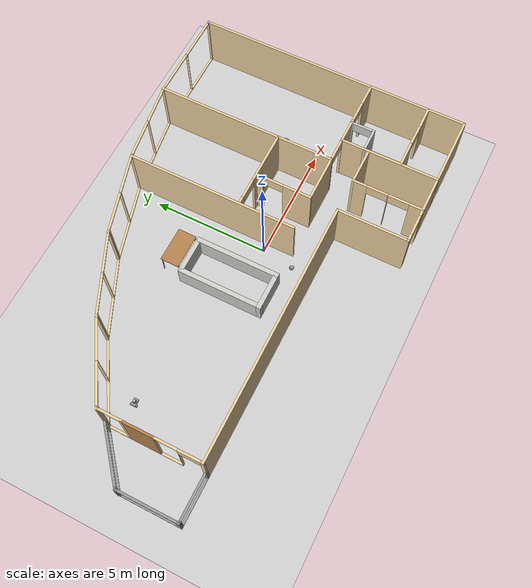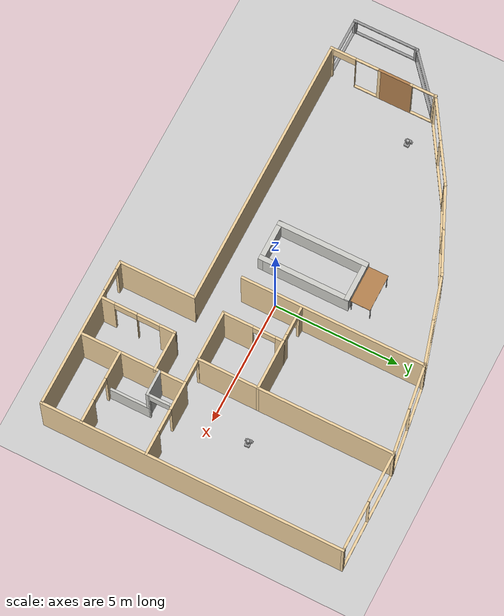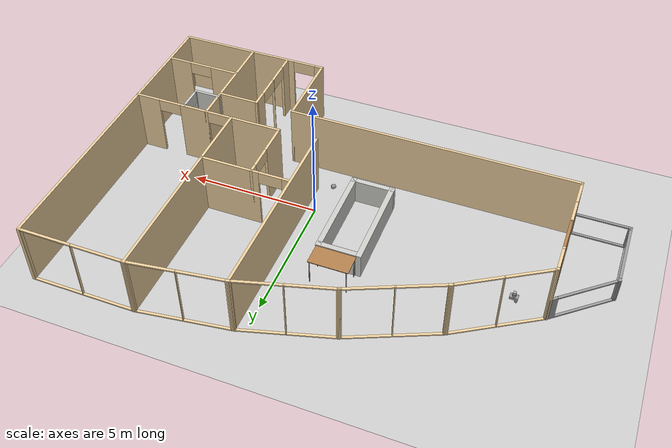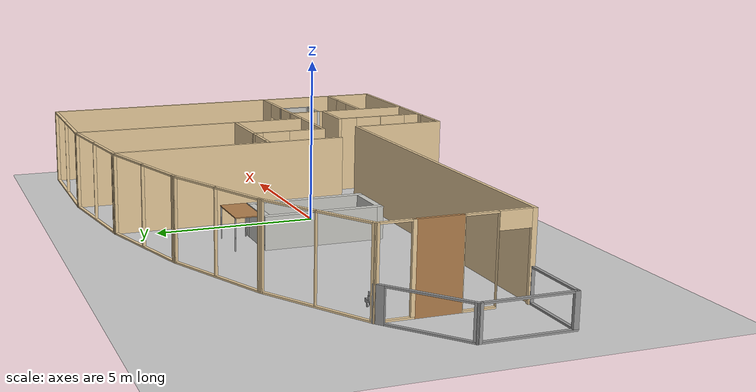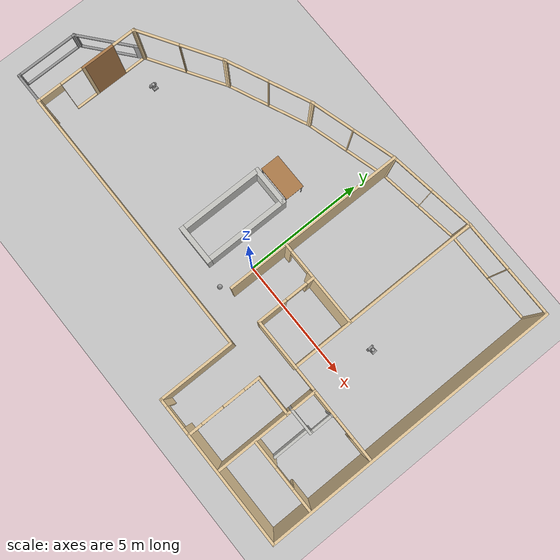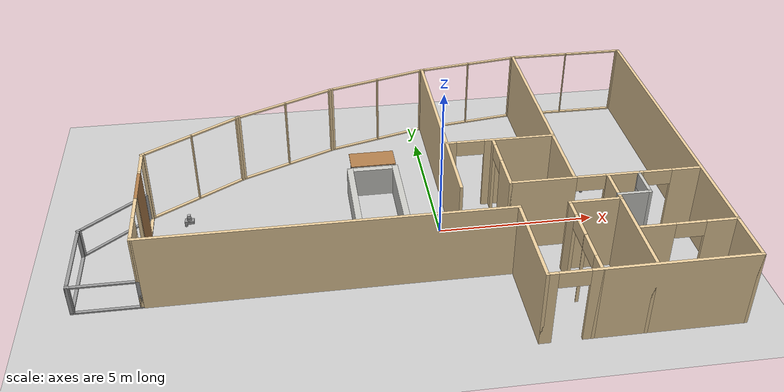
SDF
<sdf version="1.6">
 <world name="default">
  <plugin name="welcome_message" filename="libwelcome_message.so"/>
  <light name="sun" type="directional">
   <pose>0 0 10 0 -0 0</pose>
   <diffuse>0.8 0.8 0.8 1</diffuse>
   <specular>0.2 0.2 0.2 1</specular>
   <attenuation>
    <range>1000</range>
    <constant>0.9</constant>
    <linear>0.01</linear>
    <quadratic>0.001</quadratic>
   </attenuation>
   <direction>-0.5 0.1 -0.9</direction>
  </light>
  <model name="ground_plane">
   <static>1</static>
   <link name="link">
    <collision name="collision">
     <geometry><plane><normal>0 0 1</normal><size>100 100</size></plane></geometry>
     <surface>
      <contact><collide_bitmask>65535</collide_bitmask></contact>
      <friction><ode><mu>100</mu><mu2>50</mu2></ode></friction>
     </surface>
    </collision>
    <visual name="visual">
     <cast_shadows>0</cast_shadows>
     <geometry><plane><normal>0 0 1</normal><size>100 100</size></plane></geometry>
     <material>
      <script><uri>file://media/materials/scripts/gazebo.material</uri><name>Gazebo/Grey</name></script>
     </material>
    </visual>
   </link>
  </model>
  <gravity>0 0 -9.8</gravity>
  <magnetic_field>6e-06 2.3e-05 -4.2e-05</magnetic_field>
  <atmosphere type="adiabatic"/>
  <physics name="default_physics" default="0" type="ode">
   <max_step_size>0.001</max_step_size>
   <real_time_factor>1</real_time_factor>
   <real_time_update_rate>1000</real_time_update_rate>
  </physics>
  <scene><ambient>0.4 0.4 0.4 1</ambient><background>0.7 0.7 0.7 1</background><shadows>1</shadows></scene>
  <spherical_coordinates>
   <surface_model>EARTH_WGS84</surface_model>
   <latitude_deg>0</latitude_deg>
   <longitude_deg>0</longitude_deg>
   <elevation>0</elevation>
   <heading_deg>0</heading_deg>
  </spherical_coordinates>
  <model name="enso_mono">
   <pose>-1.65343 0.66639 0 0 -0 0</pose>
   <link name="Wall_0">
    <pose>7.50522 5.99675 0 0 -0 3.14159</pose>
    <visual name="Wall_0_Visual_0">
     <pose>-1.98 0 1.25 0 -0 0</pose>
     <geometry><box><size>0.14 0.1 2.5</size></box></geometry>
     <material>
      <script><uri>file://media/materials/scripts/gazebo.material</uri><name>Gazebo/Grey</name></script>
      <ambient>0.921569 0.807843 0.615686 1</ambient>
     </material>
     <meta><layer>0</layer></meta>
    </visual>
    <collision name="Wall_0_Collision_0">
     <geometry><box><size>0.14 0.1 2.5</size></box></geometry>
     <pose>-1.98 0 1.25 0 -0 0</pose>
    </collision>
    <visual name="Wall_0_Visual_1">
     <pose>0.07 0 0.025 0 -0 0</pose>
     <geometry><box><size>3.96 0.1 0.05</size></box></geometry>
     <material>
      <script><uri>file://media/materials/scripts/gazebo.material</uri><name>Gazebo/Grey</name></script>
      <ambient>0.921569 0.807843 0.615686 1</ambient>
     </material>
     <meta><layer>0</layer></meta>
    </visual>
    <collision name="Wall_0_Collision_1">
     <geometry><box><size>3.96 0.1 0.05</size></box></geometry>
     <pose>0.07 0 0.025 0 -0 0</pose>
    </collision>
    <visual name="Wall_0_Visual_2">
     <pose>0 0 1.275 0 -0 0</pose>
     <geometry><box><size>0.02 0.1 2.45</size></box></geometry>
     <material>
      <script><uri>file://media/materials/scripts/gazebo.material</uri><name>Gazebo/Grey</name></script>
      <ambient>0.921569 0.807843 0.615686 1</ambient>
     </material>
     <meta><layer>0</layer></meta>
    </visual>
    <collision name="Wall_0_Collision_2">
     <geometry><box><size>0.02 0.1 2.45</size></box></geometry>
     <pose>0 0 1.275 0 -0 0</pose>
    </collision>
    <visual name="Wall_0_Visual_3">
     <pose>1.98 0 1.275 0 -0 0</pose>
     <geometry><box><size>0.14 0.1 2.45</size></box></geometry>
     <material>
      <script><uri>file://media/materials/scripts/gazebo.material</uri><name>Gazebo/Grey</name></script>
      <ambient>0.921569 0.807843 0.615686 1</ambient>
     </material>
     <meta><layer>0</layer></meta>
    </visual>
    <collision name="Wall_0_Collision_3">
     <geometry><box><size>0.14 0.1 2.45</size></box></geometry>
     <pose>1.98 0 1.275 0 -0 0</pose>
    </collision>
    <visual name="Wall_0_Visual_4">
     <pose>-0.96 0 2.475 0 -0 0</pose>
     <geometry><box><size>1.9 0.1 0.05</size></box></geometry>
     <material>
      <script><uri>file://media/materials/scripts/gazebo.material</uri><name>Gazebo/Grey</name></script>
      <ambient>0.921569 0.807843 0.615686 1</ambient>
     </material>
     <meta><layer>0</layer></meta>
    </visual>
    <collision name="Wall_0_Collision_4">
     <geometry><box><size>1.9 0.1 0.05</size></box></geometry>
     <pose>-0.96 0 2.475 0 -0 0</pose>
    </collision>
    <visual name="Wall_0_Visual_5">
     <pose>0.96 0 2.475 0 -0 0</pose>
     <geometry><box><size>1.9 0.1 0.05</size></box></geometry>
     <material>
      <script><uri>file://media/materials/scripts/gazebo.material</uri><name>Gazebo/Grey</name></script>
      <ambient>0.921569 0.807843 0.615686 1</ambient>
     </material>
     <meta><layer>0</layer></meta>
    </visual>
    <collision name="Wall_0_Collision_5">
     <geometry><box><size>1.9 0.1 0.05</size></box></geometry>
     <pose>0.96 0 2.475 0 -0 0</pose>
    </collision>
   </link>
   <link name="Wall_1">
    <pose>3.77022 5.75175 0 0 0 -3.00131</pose>
    <visual name="Wall_1_Visual_0">
     <pose>-1.73504 0 1.25 0 -0 0</pose>
     <geometry><box><size>0.134336 0.1 2.5</size></box></geometry>
     <material>
      <script><uri>file://media/materials/scripts/gazebo.material</uri><name>Gazebo/Grey</name></script>
      <ambient>0.921569 0.807843 0.615686 1</ambient>
     </material>
     <meta><layer>0</layer></meta>
    </visual>
    <collision name="Wall_1_Collision_0">
     <geometry><box><size>0.134336 0.1 2.5</size></box></geometry>
     <pose>-1.73504 0 1.25 0 -0 0</pose>
    </collision>
    <visual name="Wall_1_Visual_1">
     <pose>0.067168 0 0.025 0 -0 0</pose>
     <geometry><box><size>3.47009 0.1 0.05</size></box></geometry>
     <material>
      <script><uri>file://media/materials/scripts/gazebo.material</uri><name>Gazebo/Grey</name></script>
      <ambient>0.921569 0.807843 0.615686 1</ambient>
     </material>
     <meta><layer>0</layer></meta>
    </visual>
    <collision name="Wall_1_Collision_1">
     <geometry><box><size>3.47009 0.1 0.05</size></box></geometry>
     <pose>0.067168 0 0.025 0 -0 0</pose>
    </collision>
    <visual name="Wall_1_Visual_2">
     <pose>-0.004951 0 1.275 0 -0 0</pose>
     <geometry><box><size>0.025852 0.1 2.45</size></box></geometry>
     <material>
      <script><uri>file://media/materials/scripts/gazebo.material</uri><name>Gazebo/Grey</name></script>
      <ambient>0.921569 0.807843 0.615686 1</ambient>
     </material>
     <meta><layer>0</layer></meta>
    </visual>
    <collision name="Wall_1_Collision_2">
     <geometry><box><size>0.025852 0.1 2.45</size></box></geometry>
     <pose>-0.004951 0 1.275 0 -0 0</pose>
    </collision>
    <visual name="Wall_1_Visual_3">
     <pose>1.73009 0 1.275 0 -0 0</pose>
     <geometry><box><size>0.144238 0.1 2.45</size></box></geometry>
     <material>
      <script><uri>file://media/materials/scripts/gazebo.material</uri><name>Gazebo/Grey</name></script>
      <ambient>0.921569 0.807843 0.615686 1</ambient>
     </material>
     <meta><layer>0</layer></meta>
    </visual>
    <collision name="Wall_1_Collision_3">
     <geometry><box><size>0.144238 0.1 2.45</size></box></geometry>
     <pose>1.73009 0 1.275 0 -0 0</pose>
    </collision>
    <visual name="Wall_1_Visual_4">
     <pose>-0.842877 0 2.475 0 -0 0</pose>
     <geometry><box><size>1.65 0.1 0.05</size></box></geometry>
     <material>
      <script><uri>file://media/materials/scripts/gazebo.material</uri><name>Gazebo/Grey</name></script>
      <ambient>0.921569 0.807843 0.615686 1</ambient>
     </material>
     <meta><layer>0</layer></meta>
    </visual>
    <collision name="Wall_1_Collision_4">
     <geometry><box><size>1.65 0.1 0.05</size></box></geometry>
     <pose>-0.842877 0 2.475 0 -0 0</pose>
    </collision>
    <visual name="Wall_1_Visual_5">
     <pose>0.832975 0 2.475 0 -0 0</pose>
     <geometry><box><size>1.65 0.1 0.05</size></box></geometry>
     <material>
      <script><uri>file://media/materials/scripts/gazebo.material</uri><name>Gazebo/Grey</name></script>
      <ambient>0.921569 0.807843 0.615686 1</ambient>
     </material>
     <meta><layer>0</layer></meta>
    </visual>
    <collision name="Wall_1_Collision_5">
     <geometry><box><size>1.65 0.1 0.05</size></box></geometry>
     <pose>0.832975 0 2.475 0 -0 0</pose>
    </collision>
   </link>
   <link name="Wall_10">
    <pose>6.50522 -6.00325 0 0 -0 0</pose>
    <visual name="Wall_10_Visual_0">
     <pose>-2.87 0 1.25 0 -0 0</pose>
     <geometry><box><size>0.36 0.1 2.5</size></box></geometry>
     <material>
      <script><uri>file://media/materials/scripts/gazebo.material</uri><name>Gazebo/Grey</name></script>
      <ambient>0.921569 0.807843 0.615686 1</ambient>
     </material>
     <meta><layer>0</layer></meta>
    </visual>
    <collision name="Wall_10_Collision_0">
     <geometry><box><size>0.36 0.1 2.5</size></box></geometry>
     <pose>-2.87 0 1.25 0 -0 0</pose>
    </collision>
    <visual name="Wall_10_Visual_1">
     <pose>0.63 0 1.25 0 -0 0</pose>
     <geometry><box><size>4.84 0.1 2.5</size></box></geometry>
     <material>
      <script><uri>file://media/materials/scripts/gazebo.material</uri><name>Gazebo/Grey</name></script>
      <ambient>0.921569 0.807843 0.615686 1</ambient>
     </material>
     <meta><layer>0</layer></meta>
    </visual>
    <collision name="Wall_10_Collision_1">
     <geometry><box><size>4.84 0.1 2.5</size></box></geometry>
     <pose>0.63 0 1.25 0 -0 0</pose>
    </collision>
    <visual name="Wall_10_Visual_2">
     <pose>-2.24 0 2.25 0 -0 0</pose>
     <geometry><box><size>0.9 0.1 0.5</size></box></geometry>
     <material>
      <script><uri>file://media/materials/scripts/gazebo.material</uri><name>Gazebo/Grey</name></script>
      <ambient>0.921569 0.807843 0.615686 1</ambient>
     </material>
     <meta><layer>0</layer></meta>
    </visual>
    <collision name="Wall_10_Collision_2">
     <geometry><box><size>0.9 0.1 0.5</size></box></geometry>
     <pose>-2.24 0 2.25 0 -0 0</pose>
    </collision>
   </link>
   <link name="Wall_11">
    <collision name="Wall_11_Collision">
     <geometry><box><size>12.1 0.1 2.5</size></box></geometry>
     <pose>0 0 1.25 0 -0 0</pose>
    </collision>
    <visual name="Wall_11_Visual">
     <pose>0 0 1.25 0 -0 0</pose>
     <geometry><box><size>12.1 0.1 2.5</size></box></geometry>
     <material>
      <script><uri>file://media/materials/scripts/gazebo.material</uri><name>Gazebo/Grey</name></script>
      <ambient>0.921569 0.807843 0.615686 1</ambient>
     </material>
     <meta><layer>0</layer></meta>
    </visual>
    <pose>9.50522 -0.00325 0 0 -0 1.5708</pose>
   </link>
   <link name="Wall_13">
    <pose>-7.49478 0.76675 0 0 0 -1.5708</pose>
    <visual name="Wall_13_Visual_0">
     <pose>-0.485 0 1.25 0 -0 0</pose>
     <geometry><box><size>0.13 0.1 2.5</size></box></geometry>
     <material>
      <script><uri>file://media/materials/scripts/gazebo.material</uri><name>Gazebo/Grey</name></script>
      <ambient>0.921569 0.807843 0.615686 1</ambient>
     </material>
     <meta><layer>0</layer></meta>
    </visual>
    <collision name="Wall_13_Collision_0">
     <geometry><box><size>0.13 0.1 2.5</size></box></geometry>
     <pose>-0.485 0 1.25 0 -0 0</pose>
    </collision>
    <visual name="Wall_13_Visual_1">
     <pose>0.065 0 0.025 0 -0 0</pose>
     <geometry><box><size>0.97 0.1 0.05</size></box></geometry>
     <material>
      <script><uri>file://media/materials/scripts/gazebo.material</uri><name>Gazebo/Grey</name></script>
      <ambient>0.921569 0.807843 0.615686 1</ambient>
     </material>
     <meta><layer>0</layer></meta>
    </visual>
    <collision name="Wall_13_Collision_1">
     <geometry><box><size>0.97 0.1 0.05</size></box></geometry>
     <pose>0.065 0 0.025 0 -0 0</pose>
    </collision>
    <visual name="Wall_13_Visual_2">
     <pose>0.495 0 1.275 0 -0 0</pose>
     <geometry><box><size>0.11 0.1 2.45</size></box></geometry>
     <material>
      <script><uri>file://media/materials/scripts/gazebo.material</uri><name>Gazebo/Grey</name></script>
      <ambient>0.921569 0.807843 0.615686 1</ambient>
     </material>
     <meta><layer>0</layer></meta>
    </visual>
    <collision name="Wall_13_Collision_2">
     <geometry><box><size>0.11 0.1 2.45</size></box></geometry>
     <pose>0.495 0 1.275 0 -0 0</pose>
    </collision>
    <visual name="Wall_13_Visual_3">
     <pose>0.01 0 2.475 0 -0 0</pose>
     <geometry><box><size>0.86 0.1 0.05</size></box></geometry>
     <material>
      <script><uri>file://media/materials/scripts/gazebo.material</uri><name>Gazebo/Grey</name></script>
      <ambient>0.921569 0.807843 0.615686 1</ambient>
     </material>
     <meta><layer>0</layer></meta>
    </visual>
    <collision name="Wall_13_Collision_3">
     <geometry><box><size>0.86 0.1 0.05</size></box></geometry>
     <pose>0.01 0 2.475 0 -0 0</pose>
    </collision>
   </link>
   <link name="Wall_15">
    <collision name="Wall_15_Collision">
     <geometry><box><size>1.37 0.1 2.5</size></box></geometry>
     <pose>0 0 1.25 0 -0 0</pose>
    </collision>
    <visual name="Wall_15_Visual">
     <pose>0 0 1.25 0 -0 0</pose>
     <geometry><box><size>1.37 0.1 2.5</size></box></geometry>
     <material>
      <script><uri>file://media/materials/scripts/gazebo.material</uri><name>Gazebo/Wood</name></script>
      <ambient>1 1 1 1</ambient>
     </material>
     <meta><layer>0</layer></meta>
    </visual>
    <pose>-7.49478 -0.368249 0 0 0 -1.5708</pose>
   </link>
   <link name="Wall_17">
    <pose>-7.49478 -2.00325 0 0 0 -1.5708</pose>
    <visual name="Wall_17_Visual_0">
     <pose>-0.99 0 1.25 0 -0 0</pose>
     <geometry><box><size>0.12 0.1 2.5</size></box></geometry>
     <material>
      <script><uri>file://media/materials/scripts/gazebo.material</uri><name>Gazebo/Grey</name></script>
      <ambient>0.921569 0.807843 0.615686 1</ambient>
     </material>
     <meta><layer>0</layer></meta>
    </visual>
    <collision name="Wall_17_Collision_0">
     <geometry><box><size>0.12 0.1 2.5</size></box></geometry>
     <pose>-0.99 0 1.25 0 -0 0</pose>
    </collision>
    <visual name="Wall_17_Visual_1">
     <pose>0.975 0 1.25 0 -0 0</pose>
     <geometry><box><size>0.149999 0.1 2.5</size></box></geometry>
     <material>
      <script><uri>file://media/materials/scripts/gazebo.material</uri><name>Gazebo/Grey</name></script>
      <ambient>0.921569 0.807843 0.615686 1</ambient>
     </material>
     <meta><layer>0</layer></meta>
    </visual>
    <collision name="Wall_17_Collision_1">
     <geometry><box><size>0.149999 0.1 2.5</size></box></geometry>
     <pose>0.975 0 1.25 0 -0 0</pose>
    </collision>
    <visual name="Wall_17_Visual_2">
     <pose>-0.465 0 0.025 0 -0 0</pose>
     <geometry><box><size>0.930001 0.1 0.05</size></box></geometry>
     <material>
      <script><uri>file://media/materials/scripts/gazebo.material</uri><name>Gazebo/Grey</name></script>
      <ambient>0.921569 0.807843 0.615686 1</ambient>
     </material>
     <meta><layer>0</layer></meta>
    </visual>
    <collision name="Wall_17_Collision_2">
     <geometry><box><size>0.930001 0.1 0.05</size></box></geometry>
     <pose>-0.465 0 0.025 0 -0 0</pose>
    </collision>
    <visual name="Wall_17_Visual_3">
     <pose>-0.005 0 1.275 0 -0 0</pose>
     <geometry><box><size>0.010001 0.1 2.45</size></box></geometry>
     <material>
      <script><uri>file://media/materials/scripts/gazebo.material</uri><name>Gazebo/Grey</name></script>
      <ambient>0.921569 0.807843 0.615686 1</ambient>
     </material>
     <meta><layer>0</layer></meta>
    </visual>
    <collision name="Wall_17_Collision_3">
     <geometry><box><size>0.010001 0.1 2.45</size></box></geometry>
     <pose>-0.005 0 1.275 0 -0 0</pose>
    </collision>
    <visual name="Wall_17_Visual_4">
     <pose>0.450001 0 2.25 0 -0 0</pose>
     <geometry><box><size>0.9 0.1 0.5</size></box></geometry>
     <material>
      <script><uri>file://media/materials/scripts/gazebo.material</uri><name>Gazebo/Grey</name></script>
      <ambient>0.921569 0.807843 0.615686 1</ambient>
     </material>
     <meta><layer>0</layer></meta>
    </visual>
    <collision name="Wall_17_Collision_4">
     <geometry><box><size>0.9 0.1 0.5</size></box></geometry>
     <pose>0.450001 0 2.25 0 -0 0</pose>
    </collision>
    <visual name="Wall_17_Visual_5">
     <pose>-0.47 0 2.475 0 -0 0</pose>
     <geometry><box><size>0.92 0.1 0.05</size></box></geometry>
     <material>
      <script><uri>file://media/materials/scripts/gazebo.material</uri><name>Gazebo/Grey</name></script>
      <ambient>0.921569 0.807843 0.615686 1</ambient>
     </material>
     <meta><layer>0</layer></meta>
    </visual>
    <collision name="Wall_17_Collision_5">
     <geometry><box><size>0.92 0.1 0.05</size></box></geometry>
     <pose>-0.47 0 2.475 0 -0 0</pose>
    </collision>
   </link>
   <link name="Wall_19">
    <collision name="Wall_19_Collision">
     <geometry><box><size>7.41 0.1 2.5</size></box></geometry>
     <pose>0 0 1.25 0 -0 0</pose>
    </collision>
    <visual name="Wall_19_Visual">
     <pose>0 0 1.25 0 -0 0</pose>
     <geometry><box><size>7.41 0.1 2.5</size></box></geometry>
     <material>
      <script><uri>file://media/materials/scripts/gazebo.material</uri><name>Gazebo/Grey</name></script>
      <ambient>0.921569 0.807843 0.615686 1</ambient>
     </material>
     <meta><layer>0</layer></meta>
    </visual>
    <pose>2.03522 1.85175 0 0 0 -1.5708</pose>
   </link>
   <link name="Wall_2">
    <pose>0.35522 5.02675 0 0 0 -2.86329</pose>
    <visual name="Wall_2_Visual_0">
     <pose>-1.72962 0 1.25 0 -0 0</pose>
     <geometry><box><size>0.135206 0.1 2.5</size></box></geometry>
     <material>
      <script><uri>file://media/materials/scripts/gazebo.material</uri><name>Gazebo/Grey</name></script>
      <ambient>0.921569 0.807843 0.615686 1</ambient>
     </material>
     <meta><layer>0</layer></meta>
    </visual>
    <collision name="Wall_2_Collision_0">
     <geometry><box><size>0.135206 0.1 2.5</size></box></geometry>
     <pose>-1.72962 0 1.25 0 -0 0</pose>
    </collision>
    <visual name="Wall_2_Visual_1">
     <pose>0.067603 0 0.025 0 -0 0</pose>
     <geometry><box><size>3.45925 0.1 0.05</size></box></geometry>
     <material>
      <script><uri>file://media/materials/scripts/gazebo.material</uri><name>Gazebo/Grey</name></script>
      <ambient>0.921569 0.807843 0.615686 1</ambient>
     </material>
     <meta><layer>0</layer></meta>
    </visual>
    <collision name="Wall_2_Collision_1">
     <geometry><box><size>3.45925 0.1 0.05</size></box></geometry>
     <pose>0.067603 0 0.025 0 -0 0</pose>
    </collision>
    <visual name="Wall_2_Visual_2">
     <pose>-0.0025 0 1.275 0 -0 0</pose>
     <geometry><box><size>0.039041 0.1 2.45</size></box></geometry>
     <material>
      <script><uri>file://media/materials/scripts/gazebo.material</uri><name>Gazebo/Grey</name></script>
      <ambient>0.921569 0.807843 0.615686 1</ambient>
     </material>
     <meta><layer>0</layer></meta>
    </visual>
    <collision name="Wall_2_Collision_2">
     <geometry><box><size>0.039041 0.1 2.45</size></box></geometry>
     <pose>-0.0025 0 1.275 0 -0 0</pose>
    </collision>
    <visual name="Wall_2_Visual_3">
     <pose>1.73212 0 1.275 0 -0 0</pose>
     <geometry><box><size>0.130206 0.1 2.45</size></box></geometry>
     <material>
      <script><uri>file://media/materials/scripts/gazebo.material</uri><name>Gazebo/Grey</name></script>
      <ambient>0.921569 0.807843 0.615686 1</ambient>
     </material>
     <meta><layer>0</layer></meta>
    </visual>
    <collision name="Wall_2_Collision_3">
     <geometry><box><size>0.130206 0.1 2.45</size></box></geometry>
     <pose>1.73212 0 1.275 0 -0 0</pose>
    </collision>
    <visual name="Wall_2_Visual_4">
     <pose>-0.84202 0 2.475 0 -0 0</pose>
     <geometry><box><size>1.64 0.1 0.05</size></box></geometry>
     <material>
      <script><uri>file://media/materials/scripts/gazebo.material</uri><name>Gazebo/Grey</name></script>
      <ambient>0.921569 0.807843 0.615686 1</ambient>
     </material>
     <meta><layer>0</layer></meta>
    </visual>
    <collision name="Wall_2_Collision_4">
     <geometry><box><size>1.64 0.1 0.05</size></box></geometry>
     <pose>-0.84202 0 2.475 0 -0 0</pose>
    </collision>
    <visual name="Wall_2_Visual_5">
     <pose>0.84202 0 2.475 0 -0 0</pose>
     <geometry><box><size>1.65 0.1 0.05</size></box></geometry>
     <material>
      <script><uri>file://media/materials/scripts/gazebo.material</uri><name>Gazebo/Grey</name></script>
      <ambient>0.921569 0.807843 0.615686 1</ambient>
     </material>
     <meta><layer>0</layer></meta>
    </visual>
    <collision name="Wall_2_Collision_5">
     <geometry><box><size>1.65 0.1 0.05</size></box></geometry>
     <pose>0.84202 0 2.475 0 -0 0</pose>
    </collision>
   </link>
   <link name="Wall_21">
    <collision name="Wall_21_Collision">
     <geometry><box><size>7.9 0.1 2.5</size></box></geometry>
     <pose>0 0 1.25 0 -0 0</pose>
    </collision>
    <visual name="Wall_21_Visual">
     <pose>0 0 1.25 0 -0 0</pose>
     <geometry><box><size>7.9 0.1 2.5</size></box></geometry>
     <material>
      <script><uri>file://media/materials/scripts/gazebo.material</uri><name>Gazebo/Grey</name></script>
      <ambient>0.921569 0.807843 0.615686 1</ambient>
     </material>
     <meta><layer>0</layer></meta>
    </visual>
    <pose>5.50522 2.09675 0 0 0 -1.5708</pose>
   </link>
   <link name="Wall_23">
    <pose>3.53522 -0.60325 0 0 0 -1.5708</pose>
    <visual name="Wall_23_Visual_0">
     <pose>-1.075 0 1.25 0 -0 0</pose>
     <geometry><box><size>0.35 0.1 2.5</size></box></geometry>
     <material>
      <script><uri>file://media/materials/scripts/gazebo.material</uri><name>Gazebo/Grey</name></script>
      <ambient>0.921569 0.807843 0.615686 1</ambient>
     </material>
     <meta><layer>0</layer></meta>
    </visual>
    <collision name="Wall_23_Collision_0">
     <geometry><box><size>0.35 0.1 2.5</size></box></geometry>
     <pose>-1.075 0 1.25 0 -0 0</pose>
    </collision>
    <visual name="Wall_23_Visual_1">
     <pose>0.625 0 1.25 0 -0 0</pose>
     <geometry><box><size>1.25 0.1 2.5</size></box></geometry>
     <material>
      <script><uri>file://media/materials/scripts/gazebo.material</uri><name>Gazebo/Grey</name></script>
      <ambient>0.921569 0.807843 0.615686 1</ambient>
     </material>
     <meta><layer>0</layer></meta>
    </visual>
    <collision name="Wall_23_Collision_1">
     <geometry><box><size>1.25 0.1 2.5</size></box></geometry>
     <pose>0.625 0 1.25 0 -0 0</pose>
    </collision>
    <visual name="Wall_23_Visual_2">
     <pose>-0.45 0 2.25 0 -0 0</pose>
     <geometry><box><size>0.9 0.1 0.5</size></box></geometry>
     <material>
      <script><uri>file://media/materials/scripts/gazebo.material</uri><name>Gazebo/Grey</name></script>
      <ambient>0.921569 0.807843 0.615686 1</ambient>
     </material>
     <meta><layer>0</layer></meta>
    </visual>
    <collision name="Wall_23_Collision_2">
     <geometry><box><size>0.9 0.1 0.5</size></box></geometry>
     <pose>-0.45 0 2.25 0 -0 0</pose>
    </collision>
   </link>
   <link name="Wall_25">
    <pose>5.00522 -4.50325 0 0 0 -1.5708</pose>
    <visual name="Wall_25_Visual_0">
     <pose>-1.22 0 1.25 0 -0 0</pose>
     <geometry><box><size>0.66 0.1 2.5</size></box></geometry>
     <material>
      <script><uri>file://media/materials/scripts/gazebo.material</uri><name>Gazebo/Grey</name></script>
      <ambient>0.921569 0.807843 0.615686 1</ambient>
     </material>
     <meta><layer>0</layer></meta>
    </visual>
    <collision name="Wall_25_Collision_0">
     <geometry><box><size>0.66 0.1 2.5</size></box></geometry>
     <pose>-1.22 0 1.25 0 -0 0</pose>
    </collision>
    <visual name="Wall_25_Visual_1">
     <pose>0.02 0 1.25 0 -0 0</pose>
     <geometry><box><size>0.02 0.1 2.5</size></box></geometry>
     <material>
      <script><uri>file://media/materials/scripts/gazebo.material</uri><name>Gazebo/Grey</name></script>
      <ambient>0.921569 0.807843 0.615686 1</ambient>
     </material>
     <meta><layer>0</layer></meta>
    </visual>
    <collision name="Wall_25_Collision_1">
     <geometry><box><size>0.02 0.1 2.5</size></box></geometry>
     <pose>0.02 0 1.25 0 -0 0</pose>
    </collision>
    <visual name="Wall_25_Visual_2">
     <pose>1.24 0 1.25 0 -0 0</pose>
     <geometry><box><size>0.62 0.1 2.5</size></box></geometry>
     <material>
      <script><uri>file://media/materials/scripts/gazebo.material</uri><name>Gazebo/Grey</name></script>
      <ambient>0.921569 0.807843 0.615686 1</ambient>
     </material>
     <meta><layer>0</layer></meta>
    </visual>
    <collision name="Wall_25_Collision_2">
     <geometry><box><size>0.62 0.1 2.5</size></box></geometry>
     <pose>1.24 0 1.25 0 -0 0</pose>
    </collision>
    <visual name="Wall_25_Visual_3">
     <pose>-0.44 0 2.25 0 -0 0</pose>
     <geometry><box><size>0.9 0.1 0.5</size></box></geometry>
     <material>
      <script><uri>file://media/materials/scripts/gazebo.material</uri><name>Gazebo/Grey</name></script>
      <ambient>0.921569 0.807843 0.615686 1</ambient>
     </material>
     <meta><layer>0</layer></meta>
    </visual>
    <collision name="Wall_25_Collision_3">
     <geometry><box><size>0.9 0.1 0.5</size></box></geometry>
     <pose>-0.44 0 2.25 0 -0 0</pose>
    </collision>
    <visual name="Wall_25_Visual_4">
     <pose>0.48 0 2.25 0 -0 0</pose>
     <geometry><box><size>0.9 0.1 0.5</size></box></geometry>
     <material>
      <script><uri>file://media/materials/scripts/gazebo.material</uri><name>Gazebo/Grey</name></script>
      <ambient>0.921569 0.807843 0.615686 1</ambient>
     </material>
     <meta><layer>0</layer></meta>
    </visual>
    <collision name="Wall_25_Collision_4">
     <geometry><box><size>0.9 0.1 0.5</size></box></geometry>
     <pose>0.48 0 2.25 0 -0 0</pose>
    </collision>
   </link>
   <link name="Wall_29">
    <collision name="Wall_29_Collision">
     <geometry><box><size>4.3 0.1 2.5</size></box></geometry>
     <pose>0 0 1.25 0 -0 0</pose>
    </collision>
    <visual name="Wall_29_Visual">
     <pose>0 0 1.25 0 -0 0</pose>
     <geometry><box><size>4.3 0.1 2.5</size></box></geometry>
     <material>
      <script><uri>file://media/materials/scripts/gazebo.material</uri><name>Gazebo/Grey</name></script>
      <ambient>0.921569 0.807843 0.615686 1</ambient>
     </material>
     <meta><layer>0</layer></meta>
    </visual>
    <pose>6.54522 -3.90325 0 0 0 -1.5708</pose>
   </link>
   <link name="Wall_3">
    <pose>-2.92478 3.83175 0 0 0 -2.72134</pose>
    <visual name="Wall_3_Visual_0">
     <pose>-1.73562 0 1.25 0 -0 0</pose>
     <geometry><box><size>0.133735 0.1 2.5</size></box></geometry>
     <material>
      <script><uri>file://media/materials/scripts/gazebo.material</uri><name>Gazebo/Grey</name></script>
      <ambient>0.921569 0.807843 0.615686 1</ambient>
     </material>
     <meta><layer>0</layer></meta>
    </visual>
    <collision name="Wall_3_Collision_0">
     <geometry><box><size>0.133735 0.1 2.5</size></box></geometry>
     <pose>-1.73562 0 1.25 0 -0 0</pose>
    </collision>
    <visual name="Wall_3_Visual_1">
     <pose>0.066867 0 0.025 0 -0 0</pose>
     <geometry><box><size>3.47125 0.1 0.05</size></box></geometry>
     <material>
      <script><uri>file://media/materials/scripts/gazebo.material</uri><name>Gazebo/Grey</name></script>
      <ambient>0.921569 0.807843 0.615686 1</ambient>
     </material>
     <meta><layer>0</layer></meta>
    </visual>
    <collision name="Wall_3_Collision_1">
     <geometry><box><size>3.47125 0.1 0.05</size></box></geometry>
     <pose>0.066867 0 0.025 0 -0 0</pose>
    </collision>
    <visual name="Wall_3_Visual_2">
     <pose>0 0 1.275 0 -0 0</pose>
     <geometry><box><size>0.037512 0.1 2.45</size></box></geometry>
     <material>
      <script><uri>file://media/materials/scripts/gazebo.material</uri><name>Gazebo/Grey</name></script>
      <ambient>0.921569 0.807843 0.615686 1</ambient>
     </material>
     <meta><layer>0</layer></meta>
    </visual>
    <collision name="Wall_3_Collision_2">
     <geometry><box><size>0.037512 0.1 2.45</size></box></geometry>
     <pose>0 0 1.275 0 -0 0</pose>
    </collision>
    <visual name="Wall_3_Visual_3">
     <pose>1.73562 0 1.275 0 -0 0</pose>
     <geometry><box><size>0.133735 0.1 2.45</size></box></geometry>
     <material>
      <script><uri>file://media/materials/scripts/gazebo.material</uri><name>Gazebo/Grey</name></script>
      <ambient>0.921569 0.807843 0.615686 1</ambient>
     </material>
     <meta><layer>0</layer></meta>
    </visual>
    <collision name="Wall_3_Collision_3">
     <geometry><box><size>0.133735 0.1 2.45</size></box></geometry>
     <pose>1.73562 0 1.275 0 -0 0</pose>
    </collision>
    <visual name="Wall_3_Visual_4">
     <pose>-0.843756 0 2.475 0 -0 0</pose>
     <geometry><box><size>1.65 0.1 0.05</size></box></geometry>
     <material>
      <script><uri>file://media/materials/scripts/gazebo.material</uri><name>Gazebo/Grey</name></script>
      <ambient>0.921569 0.807843 0.615686 1</ambient>
     </material>
     <meta><layer>0</layer></meta>
    </visual>
    <collision name="Wall_3_Collision_4">
     <geometry><box><size>1.65 0.1 0.05</size></box></geometry>
     <pose>-0.843756 0 2.475 0 -0 0</pose>
    </collision>
    <visual name="Wall_3_Visual_5">
     <pose>0.843756 0 2.475 0 -0 0</pose>
     <geometry><box><size>1.65 0.1 0.05</size></box></geometry>
     <material>
      <script><uri>file://media/materials/scripts/gazebo.material</uri><name>Gazebo/Grey</name></script>
      <ambient>0.921569 0.807843 0.615686 1</ambient>
     </material>
     <meta><layer>0</layer></meta>
    </visual>
    <collision name="Wall_3_Collision_5">
     <geometry><box><size>1.65 0.1 0.05</size></box></geometry>
     <pose>0.843756 0 2.475 0 -0 0</pose>
    </collision>
   </link>
   <link name="Wall_31">
    <pose>6.52022 -1.80325 0 0 -0 0</pose>
    <visual name="Wall_31_Visual_0">
     <pose>-1.99 0 1.25 0 -0 0</pose>
     <geometry><box><size>2.09 0.1 2.5</size></box></geometry>
     <material>
      <script><uri>file://media/materials/scripts/gazebo.material</uri><name>Gazebo/Grey</name></script>
      <ambient>0.921569 0.807843 0.615686 1</ambient>
     </material>
     <meta><layer>0</layer></meta>
    </visual>
    <collision name="Wall_31_Collision_0">
     <geometry><box><size>2.09 0.1 2.5</size></box></geometry>
     <pose>-1.99 0 1.25 0 -0 0</pose>
    </collision>
    <visual name="Wall_31_Visual_1">
     <pose>0.545 0 1.25 0 -0 0</pose>
     <geometry><box><size>1.18 0.1 2.5</size></box></geometry>
     <material>
      <script><uri>file://media/materials/scripts/gazebo.material</uri><name>Gazebo/Grey</name></script>
      <ambient>0.921569 0.807843 0.615686 1</ambient>
     </material>
     <meta><layer>0</layer></meta>
    </visual>
    <collision name="Wall_31_Collision_1">
     <geometry><box><size>1.18 0.1 2.5</size></box></geometry>
     <pose>0.545 0 1.25 0 -0 0</pose>
    </collision>
    <visual name="Wall_31_Visual_2">
     <pose>2.535 0 1.25 0 -0 0</pose>
     <geometry><box><size>1 0.1 2.5</size></box></geometry>
     <material>
      <script><uri>file://media/materials/scripts/gazebo.material</uri><name>Gazebo/Grey</name></script>
      <ambient>0.921569 0.807843 0.615686 1</ambient>
     </material>
     <meta><layer>0</layer></meta>
    </visual>
    <collision name="Wall_31_Collision_2">
     <geometry><box><size>1 0.1 2.5</size></box></geometry>
     <pose>2.535 0 1.25 0 -0 0</pose>
    </collision>
    <visual name="Wall_31_Visual_3">
     <pose>-0.495 0 2.25 0 -0 0</pose>
     <geometry><box><size>0.9 0.1 0.5</size></box></geometry>
     <material>
      <script><uri>file://media/materials/scripts/gazebo.material</uri><name>Gazebo/Grey</name></script>
      <ambient>0.921569 0.807843 0.615686 1</ambient>
     </material>
     <meta><layer>0</layer></meta>
    </visual>
    <collision name="Wall_31_Collision_3">
     <geometry><box><size>0.9 0.1 0.5</size></box></geometry>
     <pose>-0.495 0 2.25 0 -0 0</pose>
    </collision>
    <visual name="Wall_31_Visual_4">
     <pose>1.585 0 2.25 0 -0 0</pose>
     <geometry><box><size>0.9 0.1 0.5</size></box></geometry>
     <material>
      <script><uri>file://media/materials/scripts/gazebo.material</uri><name>Gazebo/Grey</name></script>
      <ambient>0.921569 0.807843 0.615686 1</ambient>
     </material>
     <meta><layer>0</layer></meta>
    </visual>
    <collision name="Wall_31_Collision_4">
     <geometry><box><size>0.9 0.1 0.5</size></box></geometry>
     <pose>1.585 0 2.25 0 -0 0</pose>
    </collision>
   </link>
   <link name="Wall_33">
    <collision name="Wall_33_Collision">
     <geometry><box><size>1.64 0.1 2.5</size></box></geometry>
     <pose>0 0 1.25 0 -0 0</pose>
    </collision>
    <visual name="Wall_33_Visual">
     <pose>0 0 1.25 0 -0 0</pose>
     <geometry><box><size>1.64 0.1 2.5</size></box></geometry>
     <material>
      <script><uri>file://media/materials/scripts/gazebo.material</uri><name>Gazebo/Grey</name></script>
      <ambient>0.921569 0.807843 0.615686 1</ambient>
     </material>
     <meta><layer>0</layer></meta>
    </visual>
    <pose>5.77522 -3.00325 0 0 -0 0</pose>
   </link>
   <link name="Wall_35">
    <collision name="Wall_35_Collision">
     <geometry><box><size>1.7 0.2 1</size></box></geometry>
     <pose>0 0 0.5 0 -0 0</pose>
    </collision>
    <visual name="Wall_35_Visual">
     <pose>0 0 0.5 0 -0 0</pose>
     <geometry><box><size>1.7 0.2 1</size></box></geometry>
     <material>
      <script><uri>file://media/materials/scripts/gazebo.material</uri><name>Gazebo/CeilingTiled</name></script>
      <ambient>1 1 1 1</ambient>
     </material>
     <meta><layer>0</layer></meta>
    </visual>
    <pose>-0.21478 -1.80325 0 0 -0 3.14159</pose>
   </link>
   <link name="Wall_37">
    <pose>8.02522 -4.40325 0 0 -0 0</pose>
    <visual name="Wall_37_Visual_0">
     <pose>-0.945 0 1.25 0 -0 0</pose>
     <geometry><box><size>1.17 0.1 2.5</size></box></geometry>
     <material>
      <script><uri>file://media/materials/scripts/gazebo.material</uri><name>Gazebo/Grey</name></script>
      <ambient>0.921569 0.807843 0.615686 1</ambient>
     </material>
     <meta><layer>0</layer></meta>
    </visual>
    <collision name="Wall_37_Collision_0">
     <geometry><box><size>1.17 0.1 2.5</size></box></geometry>
     <pose>-0.945 0 1.25 0 -0 0</pose>
    </collision>
    <visual name="Wall_37_Visual_1">
     <pose>1.035 0 1.25 0 -0 0</pose>
     <geometry><box><size>0.990001 0.1 2.5</size></box></geometry>
     <material>
      <script><uri>file://media/materials/scripts/gazebo.material</uri><name>Gazebo/Grey</name></script>
      <ambient>0.921569 0.807843 0.615686 1</ambient>
     </material>
     <meta><layer>0</layer></meta>
    </visual>
    <collision name="Wall_37_Collision_1">
     <geometry><box><size>0.990001 0.1 2.5</size></box></geometry>
     <pose>1.035 0 1.25 0 -0 0</pose>
    </collision>
    <visual name="Wall_37_Visual_2">
     <pose>0.089999 0 2.25 0 -0 0</pose>
     <geometry><box><size>0.9 0.1 0.5</size></box></geometry>
     <material>
      <script><uri>file://media/materials/scripts/gazebo.material</uri><name>Gazebo/Grey</name></script>
      <ambient>0.921569 0.807843 0.615686 1</ambient>
     </material>
     <meta><layer>0</layer></meta>
    </visual>
    <collision name="Wall_37_Collision_2">
     <geometry><box><size>0.9 0.1 0.5</size></box></geometry>
     <pose>0.089999 0 2.25 0 -0 0</pose>
    </collision>
   </link>
   <link name="Wall_39">
    <pose>3.77022 0.59675 0 0 -0 0</pose>
    <visual name="Wall_39_Visual_0">
     <pose>-1.6 0 1.25 0 -0 0</pose>
     <geometry><box><size>0.37 0.1 2.5</size></box></geometry>
     <material>
      <script><uri>file://media/materials/scripts/gazebo.material</uri><name>Gazebo/Grey</name></script>
      <ambient>0.921569 0.807843 0.615686 1</ambient>
     </material>
     <meta><layer>0</layer></meta>
    </visual>
    <collision name="Wall_39_Collision_0">
     <geometry><box><size>0.37 0.1 2.5</size></box></geometry>
     <pose>-1.6 0 1.25 0 -0 0</pose>
    </collision>
    <visual name="Wall_39_Visual_1">
     <pose>0.635 0 1.25 0 -0 0</pose>
     <geometry><box><size>2.3 0.1 2.5</size></box></geometry>
     <material>
      <script><uri>file://media/materials/scripts/gazebo.material</uri><name>Gazebo/Grey</name></script>
      <ambient>0.921569 0.807843 0.615686 1</ambient>
     </material>
     <meta><layer>0</layer></meta>
    </visual>
    <collision name="Wall_39_Collision_1">
     <geometry><box><size>2.3 0.1 2.5</size></box></geometry>
     <pose>0.635 0 1.25 0 -0 0</pose>
    </collision>
    <visual name="Wall_39_Visual_2">
     <pose>-0.965 0 2.25 0 -0 0</pose>
     <geometry><box><size>0.9 0.1 0.5</size></box></geometry>
     <material>
      <script><uri>file://media/materials/scripts/gazebo.material</uri><name>Gazebo/Grey</name></script>
      <ambient>0.921569 0.807843 0.615686 1</ambient>
     </material>
     <meta><layer>0</layer></meta>
    </visual>
    <collision name="Wall_39_Collision_2">
     <geometry><box><size>0.9 0.1 0.5</size></box></geometry>
     <pose>-0.965 0 2.25 0 -0 0</pose>
    </collision>
   </link>
   <link name="Wall_4">
    <pose>-6.00978 2.19175 0 0 0 -2.58451</pose>
    <visual name="Wall_4_Visual_0">
     <pose>-1.73335 0 1.25 0 -0 0</pose>
     <geometry><box><size>0.132359 0.1 2.5</size></box></geometry>
     <material>
      <script><uri>file://media/materials/scripts/gazebo.material</uri><name>Gazebo/Grey</name></script>
      <ambient>0.921569 0.807843 0.615686 1</ambient>
     </material>
     <meta><layer>0</layer></meta>
    </visual>
    <collision name="Wall_4_Collision_0">
     <geometry><box><size>0.132359 0.1 2.5</size></box></geometry>
     <pose>-1.73335 0 1.25 0 -0 0</pose>
    </collision>
    <visual name="Wall_4_Visual_1">
     <pose>0.066179 0 0.025 0 -0 0</pose>
     <geometry><box><size>3.4667 0.1 0.05</size></box></geometry>
     <material>
      <script><uri>file://media/materials/scripts/gazebo.material</uri><name>Gazebo/Grey</name></script>
      <ambient>0.921569 0.807843 0.615686 1</ambient>
     </material>
     <meta><layer>0</layer></meta>
    </visual>
    <collision name="Wall_4_Collision_1">
     <geometry><box><size>3.4667 0.1 0.05</size></box></geometry>
     <pose>0.066179 0 0.025 0 -0 0</pose>
    </collision>
    <visual name="Wall_4_Visual_2">
     <pose>-0.004244 0 1.275 0 -0 0</pose>
     <geometry><box><size>0.025851 0.1 2.45</size></box></geometry>
     <material>
      <script><uri>file://media/materials/scripts/gazebo.material</uri><name>Gazebo/Grey</name></script>
      <ambient>0.921569 0.807843 0.615686 1</ambient>
     </material>
     <meta><layer>0</layer></meta>
    </visual>
    <collision name="Wall_4_Collision_2">
     <geometry><box><size>0.025851 0.1 2.45</size></box></geometry>
     <pose>-0.004244 0 1.275 0 -0 0</pose>
    </collision>
    <visual name="Wall_4_Visual_3">
     <pose>1.7291 0 1.275 0 -0 0</pose>
     <geometry><box><size>0.140847 0.1 2.45</size></box></geometry>
     <material>
      <script><uri>file://media/materials/scripts/gazebo.material</uri><name>Gazebo/Grey</name></script>
      <ambient>0.921569 0.807843 0.615686 1</ambient>
     </material>
     <meta><layer>0</layer></meta>
    </visual>
    <collision name="Wall_4_Collision_3">
     <geometry><box><size>0.140847 0.1 2.45</size></box></geometry>
     <pose>1.7291 0 1.275 0 -0 0</pose>
    </collision>
    <visual name="Wall_4_Visual_4">
     <pose>-0.84217 0 2.475 0 -0 0</pose>
     <geometry><box><size>1.65 0.1 0.05</size></box></geometry>
     <material>
      <script><uri>file://media/materials/scripts/gazebo.material</uri><name>Gazebo/Grey</name></script>
      <ambient>0.921569 0.807843 0.615686 1</ambient>
     </material>
     <meta><layer>0</layer></meta>
    </visual>
    <collision name="Wall_4_Collision_4">
     <geometry><box><size>1.65 0.1 0.05</size></box></geometry>
     <pose>-0.84217 0 2.475 0 -0 0</pose>
    </collision>
    <visual name="Wall_4_Visual_5">
     <pose>0.833682 0 2.475 0 -0 0</pose>
     <geometry><box><size>1.65 0.1 0.05</size></box></geometry>
     <material>
      <script><uri>file://media/materials/scripts/gazebo.material</uri><name>Gazebo/Grey</name></script>
      <ambient>0.921569 0.807843 0.615686 1</ambient>
     </material>
     <meta><layer>0</layer></meta>
    </visual>
    <collision name="Wall_4_Collision_5">
     <geometry><box><size>1.65 0.1 0.05</size></box></geometry>
     <pose>0.833682 0 2.475 0 -0 0</pose>
    </collision>
   </link>
   <link name="Wall_41">
    <collision name="Wall_41_Collision">
     <geometry><box><size>1.673 0.2 1</size></box></geometry>
     <pose>0 0 0.5 0 -0 0</pose>
    </collision>
    <visual name="Wall_41_Visual">
     <pose>0 0 0.5 0 -0 0</pose>
     <geometry><box><size>1.673 0.2 1</size></box></geometry>
     <material>
      <script><uri>file://media/materials/scripts/gazebo.material</uri><name>Gazebo/CeilingTiled</name></script>
      <ambient>1 1 1 1</ambient>
     </material>
     <meta><layer>0</layer></meta>
    </visual>
    <pose>-0.22828 1.69675 0 0 -0 0</pose>
   </link>
   <link name="Wall_43">
    <collision name="Wall_43_Collision">
     <geometry><box><size>3.7 0.2 1</size></box></geometry>
     <pose>0 0 0.5 0 -0 0</pose>
    </collision>
    <visual name="Wall_43_Visual">
     <pose>0 0 0.5 0 -0 0</pose>
     <geometry><box><size>3.7 0.2 1</size></box></geometry>
     <material>
      <script><uri>file://media/materials/scripts/gazebo.material</uri><name>Gazebo/CeilingTiled</name></script>
      <ambient>1 1 1 1</ambient>
     </material>
     <meta><layer>0</layer></meta>
    </visual>
    <pose>-0.96478 -0.053249 0 0 -0 1.5708</pose>
   </link>
   <link name="Wall_45">
    <collision name="Wall_45_Collision">
     <geometry><box><size>3.7 0.2 1</size></box></geometry>
     <pose>0 0 0.5 0 -0 0</pose>
    </collision>
    <visual name="Wall_45_Visual">
     <pose>0 0 0.5 0 -0 0</pose>
     <geometry><box><size>3.7 0.2 1</size></box></geometry>
     <material>
      <script><uri>file://media/materials/scripts/gazebo.material</uri><name>Gazebo/CeilingTiled</name></script>
      <ambient>1 1 1 1</ambient>
     </material>
     <meta><layer>0</layer></meta>
    </visual>
    <pose>0.53522 -0.053249 0 0 0 -1.5708</pose>
   </link>
   <link name="Wall_47">
    <collision name="Wall_47_Collision">
     <geometry><box><size>1.06 0.1 2.5</size></box></geometry>
     <pose>0 0 1.25 0 -0 0</pose>
    </collision>
    <visual name="Wall_47_Visual">
     <pose>0 0 1.25 0 -0 0</pose>
     <geometry><box><size>1.06 0.1 2.5</size></box></geometry>
     <material>
      <script><uri>file://media/materials/scripts/gazebo.material</uri><name>Gazebo/CeilingTiled</name></script>
      <ambient>0.921569 0.807843 0.615686 1</ambient>
     </material>
     <meta><layer>0</layer></meta>
    </visual>
    <pose>7.02522 -2.80325 0 0 -0 0</pose>
   </link>
   <link name="Wall_49">
    <pose>7.50522 -2.30325 0 0 0 -1.5708</pose>
    <visual name="Wall_49_Visual_0">
     <pose>-0.475 0 1.25 0 -0 0</pose>
     <geometry><box><size>0.15 0.1 2.5</size></box></geometry>
     <material>
      <script><uri>file://media/materials/scripts/gazebo.material</uri><name>Gazebo/CeilingTiled</name></script>
      <ambient>1 1 1 1</ambient>
     </material>
     <meta><layer>0</layer></meta>
    </visual>
    <collision name="Wall_49_Collision_0">
     <geometry><box><size>0.15 0.1 2.5</size></box></geometry>
     <pose>-0.475 0 1.25 0 -0 0</pose>
    </collision>
    <visual name="Wall_49_Visual_1">
     <pose>0.475 0 1.25 0 -0 0</pose>
     <geometry><box><size>0.15 0.1 2.5</size></box></geometry>
     <material>
      <script><uri>file://media/materials/scripts/gazebo.material</uri><name>Gazebo/CeilingTiled</name></script>
      <ambient>1 1 1 1</ambient>
     </material>
     <meta><layer>0</layer></meta>
    </visual>
    <collision name="Wall_49_Collision_1">
     <geometry><box><size>0.15 0.1 2.5</size></box></geometry>
     <pose>0.475 0 1.25 0 -0 0</pose>
    </collision>
    <visual name="Wall_49_Visual_2">
     <pose>0 0 2.25 0 -0 0</pose>
     <geometry><box><size>0.8 0.1 0.5</size></box></geometry>
     <material>
      <script><uri>file://media/materials/scripts/gazebo.material</uri><name>Gazebo/CeilingTiled</name></script>
      <ambient>1 1 1 1</ambient>
     </material>
     <meta><layer>0</layer></meta>
    </visual>
    <collision name="Wall_49_Collision_2">
     <geometry><box><size>0.8 0.1 0.5</size></box></geometry>
     <pose>0 0 2.25 0 -0 0</pose>
    </collision>
   </link>
   <link name="Wall_5">
    <pose>-8.48978 0.43175 0 0 0 -2.4434</pose>
    <visual name="Wall_5_Visual_0">
     <pose>-1.18992 0 0.5 0 -0 0</pose>
     <geometry><box><size>0.318053 0.1 1</size></box></geometry>
     <material>
      <script><uri>file://media/materials/scripts/gazebo.material</uri><name>Gazebo/Grey</name></script>
      <ambient>1 1 1 1</ambient>
     </material>
     <meta><layer>0</layer></meta>
    </visual>
    <collision name="Wall_5_Collision_0">
     <geometry><box><size>0.318053 0.1 1</size></box></geometry>
     <pose>-1.18992 0 0.5 0 -0 0</pose>
    </collision>
    <visual name="Wall_5_Visual_1">
     <pose>0.159026 0 0.025 0 -0 0</pose>
     <geometry><box><size>2.37983 0.1 0.05</size></box></geometry>
     <material>
      <script><uri>file://media/materials/scripts/gazebo.material</uri><name>Gazebo/Grey</name></script>
      <ambient>1 1 1 1</ambient>
     </material>
     <meta><layer>0</layer></meta>
    </visual>
    <collision name="Wall_5_Collision_1">
     <geometry><box><size>2.37983 0.1 0.05</size></box></geometry>
     <pose>0.159026 0 0.025 0 -0 0</pose>
    </collision>
    <visual name="Wall_5_Visual_2">
     <pose>1.27903 0 0.525 0 -0 0</pose>
     <geometry><box><size>0.139831 0.1 0.95</size></box></geometry>
     <material>
      <script><uri>file://media/materials/scripts/gazebo.material</uri><name>Gazebo/Grey</name></script>
      <ambient>1 1 1 1</ambient>
     </material>
     <meta><layer>0</layer></meta>
    </visual>
    <collision name="Wall_5_Collision_2">
     <geometry><box><size>0.139831 0.1 0.95</size></box></geometry>
     <pose>1.27903 0 0.525 0 -0 0</pose>
    </collision>
    <visual name="Wall_5_Visual_3">
     <pose>0.089111 0 0.975 0 -0 0</pose>
     <geometry><box><size>2.24 0.1 0.05</size></box></geometry>
     <material>
      <script><uri>file://media/materials/scripts/gazebo.material</uri><name>Gazebo/Grey</name></script>
      <ambient>1 1 1 1</ambient>
     </material>
     <meta><layer>0</layer></meta>
    </visual>
    <collision name="Wall_5_Collision_3">
     <geometry><box><size>2.24 0.1 0.05</size></box></geometry>
     <pose>0.089111 0 0.975 0 -0 0</pose>
    </collision>
   </link>
   <link name="Wall_51">
    <collision name="Wall_51_Collision">
     <geometry><box><size>1.7 0.1 1</size></box></geometry>
     <pose>0 0 0.5 0 -0 0</pose>
    </collision>
    <visual name="Wall_51_Visual">
     <pose>0 0 0.5 0 -0 0</pose>
     <geometry><box><size>1.7 0.1 1</size></box></geometry>
     <material>
      <script><uri>file://media/materials/scripts/gazebo.material</uri><name>Gazebo/CeilingTiled</name></script>
      <ambient>1 1 1 1</ambient>
     </material>
     <meta><layer>0</layer></meta>
    </visual>
    <pose>7.50522 -3.60325 0 0 0 -1.5708</pose>
   </link>
   <link name="Wall_6">
    <pose>-9.48478 -1.70325 0 0 0 -1.5708</pose>
    <visual name="Wall_6_Visual_0">
     <pose>-1.275 0 0.5 0 -0 0</pose>
     <geometry><box><size>0.15 0.1 1</size></box></geometry>
     <material>
      <script><uri>file://media/materials/scripts/gazebo.material</uri><name>Gazebo/Grey</name></script>
      <ambient>1 1 1 1</ambient>
     </material>
     <meta><layer>0</layer></meta>
    </visual>
    <collision name="Wall_6_Collision_0">
     <geometry><box><size>0.15 0.1 1</size></box></geometry>
     <pose>-1.275 0 0.5 0 -0 0</pose>
    </collision>
    <visual name="Wall_6_Visual_1">
     <pose>0.075 0 0.025 0 -0 0</pose>
     <geometry><box><size>2.55 0.1 0.05</size></box></geometry>
     <material>
      <script><uri>file://media/materials/scripts/gazebo.material</uri><name>Gazebo/Grey</name></script>
      <ambient>1 1 1 1</ambient>
     </material>
     <meta><layer>0</layer></meta>
    </visual>
    <collision name="Wall_6_Collision_1">
     <geometry><box><size>2.55 0.1 0.05</size></box></geometry>
     <pose>0.075 0 0.025 0 -0 0</pose>
    </collision>
    <visual name="Wall_6_Visual_2">
     <pose>1.275 0 0.525 0 -0 0</pose>
     <geometry><box><size>0.15 0.1 0.95</size></box></geometry>
     <material>
      <script><uri>file://media/materials/scripts/gazebo.material</uri><name>Gazebo/Grey</name></script>
      <ambient>1 1 1 1</ambient>
     </material>
     <meta><layer>0</layer></meta>
    </visual>
    <collision name="Wall_6_Collision_2">
     <geometry><box><size>0.15 0.1 0.95</size></box></geometry>
     <pose>1.275 0 0.525 0 -0 0</pose>
    </collision>
    <visual name="Wall_6_Visual_3">
     <pose>-0 0 0.975 0 -0 0</pose>
     <geometry><box><size>2.4 0.1 0.05</size></box></geometry>
     <material>
      <script><uri>file://media/materials/scripts/gazebo.material</uri><name>Gazebo/Grey</name></script>
      <ambient>1 1 1 1</ambient>
     </material>
     <meta><layer>0</layer></meta>
    </visual>
    <collision name="Wall_6_Collision_3">
     <geometry><box><size>2.4 0.1 0.05</size></box></geometry>
     <pose>-0 0 0.975 0 -0 0</pose>
    </collision>
   </link>
   <link name="Wall_7">
    <pose>-8.48978 -3.00325 0 0 -0 0</pose>
    <visual name="Wall_7_Visual_0">
     <pose>-0.975 0 0.5 0 -0 0</pose>
     <geometry><box><size>0.14 0.1 1</size></box></geometry>
     <material>
      <script><uri>file://media/materials/scripts/gazebo.material</uri><name>Gazebo/Grey</name></script>
      <ambient>1 1 1 1</ambient>
     </material>
     <meta><layer>0</layer></meta>
    </visual>
    <collision name="Wall_7_Collision_0">
     <geometry><box><size>0.14 0.1 1</size></box></geometry>
     <pose>-0.975 0 0.5 0 -0 0</pose>
    </collision>
    <visual name="Wall_7_Visual_1">
     <pose>0.07 0 0.025 0 -0 0</pose>
     <geometry><box><size>1.95 0.1 0.05</size></box></geometry>
     <material>
      <script><uri>file://media/materials/scripts/gazebo.material</uri><name>Gazebo/Grey</name></script>
      <ambient>1 1 1 1</ambient>
     </material>
     <meta><layer>0</layer></meta>
    </visual>
    <collision name="Wall_7_Collision_1">
     <geometry><box><size>1.95 0.1 0.05</size></box></geometry>
     <pose>0.07 0 0.025 0 -0 0</pose>
    </collision>
    <visual name="Wall_7_Visual_2">
     <pose>0.99 0 0.525 0 -0 0</pose>
     <geometry><box><size>0.11 0.1 0.95</size></box></geometry>
     <material>
      <script><uri>file://media/materials/scripts/gazebo.material</uri><name>Gazebo/Grey</name></script>
      <ambient>1 1 1 1</ambient>
     </material>
     <meta><layer>0</layer></meta>
    </visual>
    <collision name="Wall_7_Collision_2">
     <geometry><box><size>0.11 0.1 0.95</size></box></geometry>
     <pose>0.99 0 0.525 0 -0 0</pose>
    </collision>
    <visual name="Wall_7_Visual_3">
     <pose>0.015 0 0.975 0 -0 0</pose>
     <geometry><box><size>1.84 0.1 0.05</size></box></geometry>
     <material>
      <script><uri>file://media/materials/scripts/gazebo.material</uri><name>Gazebo/Grey</name></script>
      <ambient>1 1 1 1</ambient>
     </material>
     <meta><layer>0</layer></meta>
    </visual>
    <collision name="Wall_7_Collision_3">
     <geometry><box><size>1.84 0.1 0.05</size></box></geometry>
     <pose>0.015 0 0.975 0 -0 0</pose>
    </collision>
   </link>
   <link name="Wall_8">
    <collision name="Wall_8_Collision">
     <geometry><box><size>11.1 0.1 2.5</size></box></geometry>
     <pose>0 0 1.25 0 -0 0</pose>
    </collision>
    <visual name="Wall_8_Visual">
     <pose>0 0 1.25 0 -0 0</pose>
     <geometry><box><size>11.1 0.1 2.5</size></box></geometry>
     <material>
      <script><uri>file://media/materials/scripts/gazebo.material</uri><name>Gazebo/Grey</name></script>
      <ambient>0.921569 0.807843 0.615686 1</ambient>
     </material>
     <meta><layer>0</layer></meta>
    </visual>
    <pose>-1.99478 -3.00325 0 0 -0 0</pose>
   </link>
   <link name="Wall_9">
    <collision name="Wall_9_Collision">
     <geometry><box><size>3.1 0.1 2.5</size></box></geometry>
     <pose>0 0 1.25 0 -0 0</pose>
    </collision>
    <visual name="Wall_9_Visual">
     <pose>0 0 1.25 0 -0 0</pose>
     <geometry><box><size>3.1 0.1 2.5</size></box></geometry>
     <material>
      <script><uri>file://media/materials/scripts/gazebo.material</uri><name>Gazebo/Grey</name></script>
      <ambient>0.921569 0.807843 0.615686 1</ambient>
     </material>
     <meta><layer>0</layer></meta>
    </visual>
    <pose>3.50522 -4.50325 0 0 0 -1.5708</pose>
   </link>
   <static>1</static>
  </model>
  <model name="test_robot">
   <link name="link_0">
    <pose>0.021878 2.7e-05 0.011 0 -0 0</pose>
    <inertial>
     <mass>1</mass>
     <inertia>
      <ixx>0.166667</ixx>
      <ixy>0</ixy>
      <ixz>0</ixz>
      <iyy>0.166667</iyy>
      <iyz>0</iyz>
      <izz>0.166667</izz>
     </inertia>
    </inertial>
    <visual name="visual">
     <geometry><box><size>0.3 0.2 0.1</size></box></geometry>
     <material>
      <lighting>1</lighting>
      <script><uri>file://media/materials/scripts/gazebo.material</uri><name>Gazebo/Grey</name></script>
      <shader type="pixel"><normal_map>__default__</normal_map></shader>
      <ambient>0.3 0.3 0.3 1</ambient>
      <diffuse>0.7 0.7 0.7 1</diffuse>
      <specular>0.01 0.01 0.01 1</specular>
      <emissive>0 0 0 1</emissive>
     </material>
    </visual>
    <collision name="collision">
     <geometry><box><size>0.3 0.2 0.1</size></box></geometry>
     <surface>
      <friction>
       <ode><mu>1</mu><mu2>1</mu2><fdir1>0 0 0</fdir1><slip1>0</slip1><slip2>0</slip2></ode>
       <torsional>
        <coefficient>1</coefficient>
        <patch_radius>0</patch_radius>
        <surface_radius>0</surface_radius>
        <use_patch_radius>1</use_patch_radius>
        <ode><slip>0</slip></ode>
       </torsional>
      </friction>
      <bounce><restitution_coefficient>0</restitution_coefficient><threshold>1e+06</threshold></bounce>
      <contact>
       <collide_without_contact>0</collide_without_contact>
       <collide_without_contact_bitmask>1</collide_without_contact_bitmask>
       <collide_bitmask>1</collide_bitmask>
       <ode>
        <soft_cfm>0</soft_cfm>
        <soft_erp>0.2</soft_erp>
        <kp>1e+13</kp>
        <kd>1</kd>
        <max_vel>0.01</max_vel>
        <min_depth>0</min_depth>
       </ode>
       <bullet>
        <split_impulse>1</split_impulse>
        <split_impulse_penetration_threshold>-0.01</split_impulse_penetration_threshold>
        <soft_cfm>0</soft_cfm>
        <soft_erp>0.2</soft_erp>
        <kp>1e+13</kp>
        <kd>1</kd>
       </bullet>
      </contact>
     </surface>
    </collision>
   </link>
   <link name="link_1">
    <pose>-0.078122 0.125027 -0.039 1.5707 -0 0</pose>
    <inertial>
     <mass>1</mass>
     <inertia><ixx>0.145833</ixx><ixy>0</ixy><ixz>0</ixz><iyy>0.145833</iyy><iyz>0</iyz><izz>0.125</izz></inertia>
    </inertial>
    <visual name="visual">
     <geometry><cylinder><radius>0.05</radius><length>0.05</length></cylinder></geometry>
     <material>
      <lighting>1</lighting>
      <script><uri>file://media/materials/scripts/gazebo.material</uri><name>Gazebo/Grey</name></script>
      <shader type="pixel"><normal_map>__default__</normal_map></shader>
      <ambient>0.3 0.3 0.3 1</ambient>
      <diffuse>0.7 0.7 0.7 1</diffuse>
      <specular>0.01 0.01 0.01 1</specular>
      <emissive>0 0 0 1</emissive>
     </material>
    </visual>
    <collision name="collision">
     <geometry><cylinder><radius>0.05</radius><length>0.05</length></cylinder></geometry>
     <surface>
      <friction>
       <ode><mu>1</mu><mu2>1</mu2><fdir1>0 0 0</fdir1><slip1>0</slip1><slip2>0</slip2></ode>
       <torsional>
        <coefficient>1</coefficient>
        <patch_radius>0</patch_radius>
        <surface_radius>0</surface_radius>
        <use_patch_radius>1</use_patch_radius>
        <ode><slip>0</slip></ode>
       </torsional>
      </friction>
      <bounce><restitution_coefficient>0</restitution_coefficient><threshold>1e+06</threshold></bounce>
      <contact>
       <collide_without_contact>0</collide_without_contact>
       <collide_without_contact_bitmask>1</collide_without_contact_bitmask>
       <collide_bitmask>1</collide_bitmask>
       <ode>
        <soft_cfm>0</soft_cfm>
        <soft_erp>0.2</soft_erp>
        <kp>1e+13</kp>
        <kd>1</kd>
        <max_vel>0.01</max_vel>
        <min_depth>0</min_depth>
       </ode>
       <bullet>
        <split_impulse>1</split_impulse>
        <split_impulse_penetration_threshold>-0.01</split_impulse_penetration_threshold>
        <soft_cfm>0</soft_cfm>
        <soft_erp>0.2</soft_erp>
        <kp>1e+13</kp>
        <kd>1</kd>
       </bullet>
      </contact>
     </surface>
    </collision>
   </link>
   <link name="link_1_clone">
    <pose>-0.078122 -0.124973 -0.039 1.5707 -0 0</pose>
    <inertial>
     <mass>1</mass>
     <inertia><ixx>0.145833</ixx><ixy>0</ixy><ixz>0</ixz><iyy>0.145833</iyy><iyz>0</iyz><izz>0.125</izz></inertia>
    </inertial>
    <visual name="visual">
     <geometry><cylinder><radius>0.05</radius><length>0.05</length></cylinder></geometry>
     <material>
      <lighting>1</lighting>
      <script><uri>file://media/materials/scripts/gazebo.material</uri><name>Gazebo/Grey</name></script>
      <shader type="pixel"><normal_map>__default__</normal_map></shader>
      <ambient>0.3 0.3 0.3 1</ambient>
      <diffuse>0.7 0.7 0.7 1</diffuse>
      <specular>0.01 0.01 0.01 1</specular>
      <emissive>0 0 0 1</emissive>
     </material>
    </visual>
    <collision name="collision">
     <geometry><cylinder><radius>0.05</radius><length>0.05</length></cylinder></geometry>
     <surface>
      <friction>
       <ode><mu>1</mu><mu2>1</mu2><fdir1>0 0 0</fdir1><slip1>0</slip1><slip2>0</slip2></ode>
       <torsional>
        <coefficient>1</coefficient>
        <patch_radius>0</patch_radius>
        <surface_radius>0</surface_radius>
        <use_patch_radius>1</use_patch_radius>
        <ode><slip>0</slip></ode>
       </torsional>
      </friction>
      <bounce><restitution_coefficient>0</restitution_coefficient><threshold>1e+06</threshold></bounce>
      <contact>
       <collide_without_contact>0</collide_without_contact>
       <collide_without_contact_bitmask>1</collide_without_contact_bitmask>
       <collide_bitmask>1</collide_bitmask>
       <ode>
        <soft_cfm>0</soft_cfm>
        <soft_erp>0.2</soft_erp>
        <kp>1e+13</kp>
        <kd>1</kd>
        <max_vel>0.01</max_vel>
        <min_depth>0</min_depth>
       </ode>
       <bullet>
        <split_impulse>1</split_impulse>
        <split_impulse_penetration_threshold>-0.01</split_impulse_penetration_threshold>
        <soft_cfm>0</soft_cfm>
        <soft_erp>0.2</soft_erp>
        <kp>1e+13</kp>
        <kd>1</kd>
       </bullet>
      </contact>
     </surface>
    </collision>
   </link>
   <link name="link_2">
    <pose>0.121878 2.7e-05 -0.039 0 -0 0</pose>
    <inertial>
     <mass>1</mass>
     <inertia><ixx>0.1</ixx><ixy>0</ixy><ixz>0</ixz><iyy>0.1</iyy><iyz>0</iyz><izz>0.1</izz></inertia>
    </inertial>
    <visual name="visual">
     <geometry><sphere><radius>0.05</radius></sphere></geometry>
     <material>
      <lighting>1</lighting>
      <script><uri>file://media/materials/scripts/gazebo.material</uri><name>Gazebo/Grey</name></script>
      <shader type="pixel"><normal_map>__default__</normal_map></shader>
      <ambient>0.3 0.3 0.3 1</ambient>
      <diffuse>0.7 0.7 0.7 1</diffuse>
      <specular>0.01 0.01 0.01 1</specular>
      <emissive>0 0 0 1</emissive>
     </material>
    </visual>
    <collision name="collision">
     <geometry><sphere><radius>0.05</radius></sphere></geometry>
     <surface>
      <friction>
       <ode><mu>1</mu><mu2>1</mu2><fdir1>0 0 0</fdir1><slip1>0</slip1><slip2>0</slip2></ode>
       <torsional>
        <coefficient>1</coefficient>
        <patch_radius>0</patch_radius>
        <surface_radius>0</surface_radius>
        <use_patch_radius>1</use_patch_radius>
        <ode><slip>0</slip></ode>
       </torsional>
      </friction>
      <bounce><restitution_coefficient>0</restitution_coefficient><threshold>1e+06</threshold></bounce>
      <contact>
       <collide_without_contact>0</collide_without_contact>
       <collide_without_contact_bitmask>1</collide_without_contact_bitmask>
       <collide_bitmask>1</collide_bitmask>
       <ode>
        <soft_cfm>0</soft_cfm>
        <soft_erp>0.2</soft_erp>
        <kp>1e+13</kp>
        <kd>1</kd>
        <max_vel>0.01</max_vel>
        <min_depth>0</min_depth>
       </ode>
       <bullet>
        <split_impulse>1</split_impulse>
        <split_impulse_penetration_threshold>-0.01</split_impulse_penetration_threshold>
        <soft_cfm>0</soft_cfm>
        <soft_erp>0.2</soft_erp>
        <kp>1e+13</kp>
        <kd>1</kd>
       </bullet>
      </contact>
     </surface>
    </collision>
   </link>
   <link name="link_3">
    <pose>0.021878 2.7e-05 0.111 0 -0 0</pose>
    <inertial>
     <mass>1</mass>
     <inertia><ixx>0.145833</ixx><ixy>0</ixy><ixz>0</ixz><iyy>0.145833</iyy><iyz>0</iyz><izz>0.125</izz></inertia>
    </inertial>
    <visual name="visual">
     <geometry><cylinder><radius>0.075</radius><length>0.1</length></cylinder></geometry>
     <material>
      <lighting>1</lighting>
      <script><uri>file://media/materials/scripts/gazebo.material</uri><name>Gazebo/Grey</name></script>
      <shader type="pixel"><normal_map>__default__</normal_map></shader>
      <ambient>0.3 0.3 0.3 1</ambient>
      <diffuse>0.7 0.7 0.7 1</diffuse>
      <specular>0.01 0.01 0.01 1</specular>
      <emissive>0 0 0 1</emissive>
     </material>
    </visual>
    <collision name="collision">
     <geometry><cylinder><radius>0.075</radius><length>0.1</length></cylinder></geometry>
     <surface>
      <friction>
       <ode><mu>1</mu><mu2>1</mu2><fdir1>0 0 0</fdir1><slip1>0</slip1><slip2>0</slip2></ode>
       <torsional>
        <coefficient>1</coefficient>
        <patch_radius>0</patch_radius>
        <surface_radius>0</surface_radius>
        <use_patch_radius>1</use_patch_radius>
        <ode><slip>0</slip></ode>
       </torsional>
      </friction>
      <bounce><restitution_coefficient>0</restitution_coefficient><threshold>1e+06</threshold></bounce>
      <contact>
       <collide_without_contact>0</collide_without_contact>
       <collide_without_contact_bitmask>1</collide_without_contact_bitmask>
       <collide_bitmask>1</collide_bitmask>
       <ode>
        <soft_cfm>0</soft_cfm>
        <soft_erp>0.2</soft_erp>
        <kp>1e+13</kp>
        <kd>1</kd>
        <max_vel>0.01</max_vel>
        <min_depth>0</min_depth>
       </ode>
       <bullet>
        <split_impulse>1</split_impulse>
        <split_impulse_penetration_threshold>-0.01</split_impulse_penetration_threshold>
        <soft_cfm>0</soft_cfm>
        <soft_erp>0.2</soft_erp>
        <kp>1e+13</kp>
        <kd>1</kd>
       </bullet>
      </contact>
     </surface>
    </collision>
   </link>
   <model name="depth_camera">
    <link name="link">
     <pose>0 0 0.05 0 -0 0</pose>
     <inertial>
      <mass>0.1</mass>
      <inertia>
       <ixx>0.000166667</ixx>
       <iyy>0.000166667</iyy>
       <izz>0.000166667</izz>
       <ixy>0</ixy>
       <ixz>0</ixz>
       <iyz>0</iyz>
      </inertia>
     </inertial>
     <collision name="collision"><geometry><box><size>0.1 0.1 0.1</size></box></geometry></collision>
     <visual name="visual"><geometry><box><size>0.1 0.1 0.1</size></box></geometry></visual>
     <sensor name="camera" type="depth">
      <camera name="__default__">
       <horizontal_fov>1.047</horizontal_fov>
       <image><width>320</width><height>240</height></image>
       <clip><near>0.1</near><far>100</far></clip>
      </camera>
      <always_on>1</always_on>
      <update_rate>30</update_rate>
      <visualize>1</visualize>
     </sensor>
    </link>
    <pose>0.020611 -0.000134 0.159999 0 -0 0</pose>
   </model>
   <joint name="link_0_JOINT_0" type="revolute">
    <parent>link_0</parent>
    <child>link_1</child>
    <axis>
     <xyz>0 0 1</xyz>
     <use_parent_model_frame>0</use_parent_model_frame>
     <limit>
      <lower>-1.79769e+308</lower>
      <upper>1.79769e+308</upper>
      <effort>-1</effort>
      <velocity>-1</velocity>
     </limit>
     <dynamics>
      <spring_reference>0</spring_reference>
      <spring_stiffness>0</spring_stiffness>
      <damping>0</damping>
     </dynamics>
    </axis>
    <physics>
     <ode><limit><cfm>0</cfm><erp>0.2</erp></limit><suspension><cfm>0</cfm><erp>0.2</erp></suspension></ode>
    </physics>
   </joint>
   <joint name="link_0_JOINT_1" type="revolute">
    <parent>link_0</parent>
    <child>link_1_clone</child>
    <axis>
     <xyz>0 0 1</xyz>
     <use_parent_model_frame>0</use_parent_model_frame>
     <limit>
      <lower>-1.79769e+308</lower>
      <upper>1.79769e+308</upper>
      <effort>-1</effort>
      <velocity>-1</velocity>
     </limit>
     <dynamics>
      <spring_reference>0</spring_reference>
      <spring_stiffness>0</spring_stiffness>
      <damping>0</damping>
     </dynamics>
    </axis>
    <physics>
     <ode><limit><cfm>0</cfm><erp>0.2</erp></limit><suspension><cfm>0</cfm><erp>0.2</erp></suspension></ode>
    </physics>
   </joint>
   <joint name="link_0_JOINT_3" type="ball">
    <parent>link_0</parent>
    <child>link_2</child>
    <physics>
     <ode><limit><cfm>0</cfm><erp>0.2</erp></limit><suspension><cfm>0</cfm><erp>0.2</erp></suspension></ode>
    </physics>
   </joint>
   <joint name="link_0_JOINT_4" type="fixed">
    <parent>link_0</parent>
    <child>link_3</child>
    <physics>
     <ode><limit><cfm>0</cfm><erp>0.2</erp></limit><suspension><cfm>0</cfm><erp>0.2</erp></suspension></ode>
    </physics>
   </joint>
   <joint name="link_3_JOINT_6" type="fixed">
    <parent>link_3</parent>
    <child>depth_camera::link</child>
    <physics>
     <ode><limit><cfm>0</cfm><erp>0.2</erp></limit><suspension><cfm>0</cfm><erp>0.2</erp></suspension></ode>
    </physics>
   </joint>
   <static>0</static>
   <pose>-7.96164 1.48292 0.089001 0 1.6e-05 -0.014993</pose>
  </model>
  <model name="test_robot_0">
   <link name="link_0">
    <pose>0.021878 2.7e-05 0.011 0 -0 0</pose>
    <inertial>
     <mass>1</mass>
     <inertia>
      <ixx>0.166667</ixx>
      <ixy>0</ixy>
      <ixz>0</ixz>
      <iyy>0.166667</iyy>
      <iyz>0</iyz>
      <izz>0.166667</izz>
     </inertia>
    </inertial>
    <visual name="visual">
     <geometry><box><size>0.3 0.2 0.1</size></box></geometry>
     <material>
      <lighting>1</lighting>
      <script><uri>file://media/materials/scripts/gazebo.material</uri><name>Gazebo/Grey</name></script>
      <shader type="pixel"><normal_map>__default__</normal_map></shader>
      <ambient>0.3 0.3 0.3 1</ambient>
      <diffuse>0.7 0.7 0.7 1</diffuse>
      <specular>0.01 0.01 0.01 1</specular>
      <emissive>0 0 0 1</emissive>
     </material>
    </visual>
    <collision name="collision">
     <geometry><box><size>0.3 0.2 0.1</size></box></geometry>
     <surface>
      <friction>
       <ode><mu>1</mu><mu2>1</mu2><fdir1>0 0 0</fdir1><slip1>0</slip1><slip2>0</slip2></ode>
       <torsional>
        <coefficient>1</coefficient>
        <patch_radius>0</patch_radius>
        <surface_radius>0</surface_radius>
        <use_patch_radius>1</use_patch_radius>
        <ode><slip>0</slip></ode>
       </torsional>
      </friction>
      <bounce><restitution_coefficient>0</restitution_coefficient><threshold>1e+06</threshold></bounce>
      <contact>
       <collide_without_contact>0</collide_without_contact>
       <collide_without_contact_bitmask>1</collide_without_contact_bitmask>
       <collide_bitmask>1</collide_bitmask>
       <ode>
        <soft_cfm>0</soft_cfm>
        <soft_erp>0.2</soft_erp>
        <kp>1e+13</kp>
        <kd>1</kd>
        <max_vel>0.01</max_vel>
        <min_depth>0</min_depth>
       </ode>
       <bullet>
        <split_impulse>1</split_impulse>
        <split_impulse_penetration_threshold>-0.01</split_impulse_penetration_threshold>
        <soft_cfm>0</soft_cfm>
        <soft_erp>0.2</soft_erp>
        <kp>1e+13</kp>
        <kd>1</kd>
       </bullet>
      </contact>
     </surface>
    </collision>
   </link>
   <link name="link_1">
    <pose>-0.078122 0.125027 -0.039 1.5707 -0 0</pose>
    <inertial>
     <mass>1</mass>
     <inertia><ixx>0.145833</ixx><ixy>0</ixy><ixz>0</ixz><iyy>0.145833</iyy><iyz>0</iyz><izz>0.125</izz></inertia>
    </inertial>
    <visual name="visual">
     <geometry><cylinder><radius>0.05</radius><length>0.05</length></cylinder></geometry>
     <material>
      <lighting>1</lighting>
      <script><uri>file://media/materials/scripts/gazebo.material</uri><name>Gazebo/Grey</name></script>
      <shader type="pixel"><normal_map>__default__</normal_map></shader>
      <ambient>0.3 0.3 0.3 1</ambient>
      <diffuse>0.7 0.7 0.7 1</diffuse>
      <specular>0.01 0.01 0.01 1</specular>
      <emissive>0 0 0 1</emissive>
     </material>
    </visual>
    <collision name="collision">
     <geometry><cylinder><radius>0.05</radius><length>0.05</length></cylinder></geometry>
     <surface>
      <friction>
       <ode><mu>1</mu><mu2>1</mu2><fdir1>0 0 0</fdir1><slip1>0</slip1><slip2>0</slip2></ode>
       <torsional>
        <coefficient>1</coefficient>
        <patch_radius>0</patch_radius>
        <surface_radius>0</surface_radius>
        <use_patch_radius>1</use_patch_radius>
        <ode><slip>0</slip></ode>
       </torsional>
      </friction>
      <bounce><restitution_coefficient>0</restitution_coefficient><threshold>1e+06</threshold></bounce>
      <contact>
       <collide_without_contact>0</collide_without_contact>
       <collide_without_contact_bitmask>1</collide_without_contact_bitmask>
       <collide_bitmask>1</collide_bitmask>
       <ode>
        <soft_cfm>0</soft_cfm>
        <soft_erp>0.2</soft_erp>
        <kp>1e+13</kp>
        <kd>1</kd>
        <max_vel>0.01</max_vel>
        <min_depth>0</min_depth>
       </ode>
       <bullet>
        <split_impulse>1</split_impulse>
        <split_impulse_penetration_threshold>-0.01</split_impulse_penetration_threshold>
        <soft_cfm>0</soft_cfm>
        <soft_erp>0.2</soft_erp>
        <kp>1e+13</kp>
        <kd>1</kd>
       </bullet>
      </contact>
     </surface>
    </collision>
   </link>
   <link name="link_1_clone">
    <pose>-0.078122 -0.124973 -0.039 1.5707 -0 0</pose>
    <inertial>
     <mass>1</mass>
     <inertia><ixx>0.145833</ixx><ixy>0</ixy><ixz>0</ixz><iyy>0.145833</iyy><iyz>0</iyz><izz>0.125</izz></inertia>
    </inertial>
    <visual name="visual">
     <geometry><cylinder><radius>0.05</radius><length>0.05</length></cylinder></geometry>
     <material>
      <lighting>1</lighting>
      <script><uri>file://media/materials/scripts/gazebo.material</uri><name>Gazebo/Grey</name></script>
      <shader type="pixel"><normal_map>__default__</normal_map></shader>
      <ambient>0.3 0.3 0.3 1</ambient>
      <diffuse>0.7 0.7 0.7 1</diffuse>
      <specular>0.01 0.01 0.01 1</specular>
      <emissive>0 0 0 1</emissive>
     </material>
    </visual>
    <collision name="collision">
     <geometry><cylinder><radius>0.05</radius><length>0.05</length></cylinder></geometry>
     <surface>
      <friction>
       <ode><mu>1</mu><mu2>1</mu2><fdir1>0 0 0</fdir1><slip1>0</slip1><slip2>0</slip2></ode>
       <torsional>
        <coefficient>1</coefficient>
        <patch_radius>0</patch_radius>
        <surface_radius>0</surface_radius>
        <use_patch_radius>1</use_patch_radius>
        <ode><slip>0</slip></ode>
       </torsional>
      </friction>
      <bounce><restitution_coefficient>0</restitution_coefficient><threshold>1e+06</threshold></bounce>
      <contact>
       <collide_without_contact>0</collide_without_contact>
       <collide_without_contact_bitmask>1</collide_without_contact_bitmask>
       <collide_bitmask>1</collide_bitmask>
       <ode>
        <soft_cfm>0</soft_cfm>
        <soft_erp>0.2</soft_erp>
        <kp>1e+13</kp>
        <kd>1</kd>
        <max_vel>0.01</max_vel>
        <min_depth>0</min_depth>
       </ode>
       <bullet>
        <split_impulse>1</split_impulse>
        <split_impulse_penetration_threshold>-0.01</split_impulse_penetration_threshold>
        <soft_cfm>0</soft_cfm>
        <soft_erp>0.2</soft_erp>
        <kp>1e+13</kp>
        <kd>1</kd>
       </bullet>
      </contact>
     </surface>
    </collision>
   </link>
   <link name="link_2">
    <pose>0.121878 2.7e-05 -0.039 0 -0 0</pose>
    <inertial>
     <mass>1</mass>
     <inertia><ixx>0.1</ixx><ixy>0</ixy><ixz>0</ixz><iyy>0.1</iyy><iyz>0</iyz><izz>0.1</izz></inertia>
    </inertial>
    <visual name="visual">
     <geometry><sphere><radius>0.05</radius></sphere></geometry>
     <material>
      <lighting>1</lighting>
      <script><uri>file://media/materials/scripts/gazebo.material</uri><name>Gazebo/Grey</name></script>
      <shader type="pixel"><normal_map>__default__</normal_map></shader>
      <ambient>0.3 0.3 0.3 1</ambient>
      <diffuse>0.7 0.7 0.7 1</diffuse>
      <specular>0.01 0.01 0.01 1</specular>
      <emissive>0 0 0 1</emissive>
     </material>
    </visual>
    <collision name="collision">
     <geometry><sphere><radius>0.05</radius></sphere></geometry>
     <surface>
      <friction>
       <ode><mu>1</mu><mu2>1</mu2><fdir1>0 0 0</fdir1><slip1>0</slip1><slip2>0</slip2></ode>
       <torsional>
        <coefficient>1</coefficient>
        <patch_radius>0</patch_radius>
        <surface_radius>0</surface_radius>
        <use_patch_radius>1</use_patch_radius>
        <ode><slip>0</slip></ode>
       </torsional>
      </friction>
      <bounce><restitution_coefficient>0</restitution_coefficient><threshold>1e+06</threshold></bounce>
      <contact>
       <collide_without_contact>0</collide_without_contact>
       <collide_without_contact_bitmask>1</collide_without_contact_bitmask>
       <collide_bitmask>1</collide_bitmask>
       <ode>
        <soft_cfm>0</soft_cfm>
        <soft_erp>0.2</soft_erp>
        <kp>1e+13</kp>
        <kd>1</kd>
        <max_vel>0.01</max_vel>
        <min_depth>0</min_depth>
       </ode>
       <bullet>
        <split_impulse>1</split_impulse>
        <split_impulse_penetration_threshold>-0.01</split_impulse_penetration_threshold>
        <soft_cfm>0</soft_cfm>
        <soft_erp>0.2</soft_erp>
        <kp>1e+13</kp>
        <kd>1</kd>
       </bullet>
      </contact>
     </surface>
    </collision>
   </link>
   <link name="link_3">
    <pose>0.021878 2.7e-05 0.111 0 -0 0</pose>
    <inertial>
     <mass>1</mass>
     <inertia><ixx>0.145833</ixx><ixy>0</ixy><ixz>0</ixz><iyy>0.145833</iyy><iyz>0</iyz><izz>0.125</izz></inertia>
    </inertial>
    <visual name="visual">
     <geometry><cylinder><radius>0.075</radius><length>0.1</length></cylinder></geometry>
     <material>
      <lighting>1</lighting>
      <script><uri>file://media/materials/scripts/gazebo.material</uri><name>Gazebo/Grey</name></script>
      <shader type="pixel"><normal_map>__default__</normal_map></shader>
      <ambient>0.3 0.3 0.3 1</ambient>
      <diffuse>0.7 0.7 0.7 1</diffuse>
      <specular>0.01 0.01 0.01 1</specular>
      <emissive>0 0 0 1</emissive>
     </material>
    </visual>
    <collision name="collision">
     <geometry><cylinder><radius>0.075</radius><length>0.1</length></cylinder></geometry>
     <surface>
      <friction>
       <ode><mu>1</mu><mu2>1</mu2><fdir1>0 0 0</fdir1><slip1>0</slip1><slip2>0</slip2></ode>
       <torsional>
        <coefficient>1</coefficient>
        <patch_radius>0</patch_radius>
        <surface_radius>0</surface_radius>
        <use_patch_radius>1</use_patch_radius>
        <ode><slip>0</slip></ode>
       </torsional>
      </friction>
      <bounce><restitution_coefficient>0</restitution_coefficient><threshold>1e+06</threshold></bounce>
      <contact>
       <collide_without_contact>0</collide_without_contact>
       <collide_without_contact_bitmask>1</collide_without_contact_bitmask>
       <collide_bitmask>1</collide_bitmask>
       <ode>
        <soft_cfm>0</soft_cfm>
        <soft_erp>0.2</soft_erp>
        <kp>1e+13</kp>
        <kd>1</kd>
        <max_vel>0.01</max_vel>
        <min_depth>0</min_depth>
       </ode>
       <bullet>
        <split_impulse>1</split_impulse>
        <split_impulse_penetration_threshold>-0.01</split_impulse_penetration_threshold>
        <soft_cfm>0</soft_cfm>
        <soft_erp>0.2</soft_erp>
        <kp>1e+13</kp>
        <kd>1</kd>
       </bullet>
      </contact>
     </surface>
    </collision>
   </link>
   <model name="depth_camera">
    <link name="link">
     <pose>0 0 0.05 0 -0 0</pose>
     <inertial>
      <mass>0.1</mass>
      <inertia>
       <ixx>0.000166667</ixx>
       <iyy>0.000166667</iyy>
       <izz>0.000166667</izz>
       <ixy>0</ixy>
       <ixz>0</ixz>
       <iyz>0</iyz>
      </inertia>
     </inertial>
     <collision name="collision"><geometry><box><size>0.1 0.1 0.1</size></box></geometry></collision>
     <visual name="visual"><geometry><box><size>0.1 0.1 0.1</size></box></geometry></visual>
     <sensor name="camera" type="depth">
      <camera name="__default__">
       <horizontal_fov>1.047</horizontal_fov>
       <image><width>320</width><height>240</height></image>
       <clip><near>0.1</near><far>100</far></clip>
      </camera>
      <always_on>1</always_on>
      <update_rate>30</update_rate>
      <visualize>1</visualize>
     </sensor>
    </link>
    <pose>0.020611 -0.000134 0.159999 0 -0 0</pose>
   </model>
   <joint name="link_0_JOINT_0" type="revolute">
    <parent>link_0</parent>
    <child>link_1</child>
    <axis>
     <xyz>0 0 1</xyz>
     <use_parent_model_frame>0</use_parent_model_frame>
     <limit>
      <lower>-1.79769e+308</lower>
      <upper>1.79769e+308</upper>
      <effort>-1</effort>
      <velocity>-1</velocity>
     </limit>
     <dynamics>
      <spring_reference>0</spring_reference>
      <spring_stiffness>0</spring_stiffness>
      <damping>0</damping>
     </dynamics>
    </axis>
    <physics>
     <ode><limit><cfm>0</cfm><erp>0.2</erp></limit><suspension><cfm>0</cfm><erp>0.2</erp></suspension></ode>
    </physics>
   </joint>
   <joint name="link_0_JOINT_1" type="revolute">
    <parent>link_0</parent>
    <child>link_1_clone</child>
    <axis>
     <xyz>0 0 1</xyz>
     <use_parent_model_frame>0</use_parent_model_frame>
     <limit>
      <lower>-1.79769e+308</lower>
      <upper>1.79769e+308</upper>
      <effort>-1</effort>
      <velocity>-1</velocity>
     </limit>
     <dynamics>
      <spring_reference>0</spring_reference>
      <spring_stiffness>0</spring_stiffness>
      <damping>0</damping>
     </dynamics>
    </axis>
    <physics>
     <ode><limit><cfm>0</cfm><erp>0.2</erp></limit><suspension><cfm>0</cfm><erp>0.2</erp></suspension></ode>
    </physics>
   </joint>
   <joint name="link_0_JOINT_3" type="ball">
    <parent>link_0</parent>
    <child>link_2</child>
    <physics>
     <ode><limit><cfm>0</cfm><erp>0.2</erp></limit><suspension><cfm>0</cfm><erp>0.2</erp></suspension></ode>
    </physics>
   </joint>
   <joint name="link_0_JOINT_4" type="fixed">
    <parent>link_0</parent>
    <child>link_3</child>
    <physics>
     <ode><limit><cfm>0</cfm><erp>0.2</erp></limit><suspension><cfm>0</cfm><erp>0.2</erp></suspension></ode>
    </physics>
   </joint>
   <joint name="link_3_JOINT_6" type="fixed">
    <parent>link_3</parent>
    <child>depth_camera::link</child>
    <physics>
     <ode><limit><cfm>0</cfm><erp>0.2</erp></limit><suspension><cfm>0</cfm><erp>0.2</erp></suspension></ode>
    </physics>
   </joint>
   <static>0</static>
   <pose>5.15587 1.53667 0.089001 -0 1.6e-05 0.093611</pose>
  </model>
  <model name="table">
   <static>1</static>
   <link name="link">
    <collision name="surface">
     <pose>0 0 1 0 -0 0</pose>
     <geometry><box><size>1.5 0.8 0.03</size></box></geometry>
     <surface><friction><ode><mu>0.6</mu><mu2>0.6</mu2></ode></friction></surface>
    </collision>
    <visual name="visual1">
     <pose>0 0 1 0 -0 0</pose>
     <geometry><box><size>1.5 0.8 0.03</size></box></geometry>
     <material>
      <script><uri>file://media/materials/scripts/gazebo.material</uri><name>Gazebo/Wood</name></script>
     </material>
    </visual>
    <collision name="front_left_leg">
     <pose>0.68 0.38 0.5 0 -0 0</pose>
     <geometry><cylinder><radius>0.02</radius><length>1</length></cylinder></geometry>
    </collision>
    <visual name="front_left_leg">
     <pose>0.68 0.38 0.5 0 -0 0</pose>
     <geometry><cylinder><radius>0.02</radius><length>1</length></cylinder></geometry>
     <material>
      <script><uri>file://media/materials/scripts/gazebo.material</uri><name>Gazebo/Grey</name></script>
     </material>
    </visual>
    <collision name="front_right_leg">
     <pose>0.68 -0.38 0.5 0 -0 0</pose>
     <geometry><cylinder><radius>0.02</radius><length>1</length></cylinder></geometry>
    </collision>
    <visual name="front_right_leg">
     <pose>0.68 -0.38 0.5 0 -0 0</pose>
     <geometry><cylinder><radius>0.02</radius><length>1</length></cylinder></geometry>
     <material>
      <script><uri>file://media/materials/scripts/gazebo.material</uri><name>Gazebo/Grey</name></script>
     </material>
    </visual>
    <collision name="back_right_leg">
     <pose>-0.68 -0.38 0.5 0 -0 0</pose>
     <geometry><cylinder><radius>0.02</radius><length>1</length></cylinder></geometry>
    </collision>
    <visual name="back_right_leg">
     <pose>-0.68 -0.38 0.5 0 -0 0</pose>
     <geometry><cylinder><radius>0.02</radius><length>1</length></cylinder></geometry>
     <material>
      <script><uri>file://media/materials/scripts/gazebo.material</uri><name>Gazebo/Grey</name></script>
     </material>
    </visual>
    <collision name="back_left_leg">
     <pose>-0.68 0.38 0.5 0 -0 0</pose>
     <geometry><cylinder><radius>0.02</radius><length>1</length></cylinder></geometry>
    </collision>
    <visual name="back_left_leg">
     <pose>-0.68 0.38 0.5 0 -0 0</pose>
     <geometry><cylinder><radius>0.02</radius><length>1</length></cylinder></geometry>
     <material>
      <script><uri>file://media/materials/scripts/gazebo.material</uri><name>Gazebo/Grey</name></script>
     </material>
    </visual>
   </link>
   <pose>-1.82096 2.91625 0 0 -0 0</pose>
  </model>
  <model name="my_ball">
   <link name="link_0">
    <inertial>
     <mass>1</mass>
     <inertia><ixx>0.1</ixx><ixy>0</ixy><ixz>0</ixz><iyy>0.1</iyy><iyz>0</iyz><izz>0.1</izz></inertia>
    </inertial>
    <visual name="visual">
     <geometry><sphere><radius>0.1</radius></sphere></geometry>
     <material>
      <lighting>1</lighting>
      <script><uri>file://media/materials/scripts/gazebo.material</uri><name>Gazebo/Grey</name></script>
      <shader type="pixel"><normal_map>__default__</normal_map></shader>
      <ambient>1 1 1 1</ambient>
      <diffuse>1 1 1 1</diffuse>
      <specular>1 1 1 1</specular>
      <emissive>1 1 1 1</emissive>
     </material>
    </visual>
    <collision name="collision">
     <geometry><sphere><radius>0.1</radius></sphere></geometry>
     <surface>
      <friction>
       <ode><mu>1</mu><mu2>1</mu2><fdir1>0 0 0</fdir1><slip1>0</slip1><slip2>0</slip2></ode>
       <torsional>
        <coefficient>1</coefficient>
        <patch_radius>0</patch_radius>
        <surface_radius>0</surface_radius>
        <use_patch_radius>1</use_patch_radius>
        <ode><slip>0</slip></ode>
       </torsional>
      </friction>
      <bounce><restitution_coefficient>0</restitution_coefficient><threshold>1e+06</threshold></bounce>
      <contact>
       <collide_without_contact>0</collide_without_contact>
       <collide_without_contact_bitmask>1</collide_without_contact_bitmask>
       <collide_bitmask>1</collide_bitmask>
       <ode>
        <soft_cfm>0</soft_cfm>
        <soft_erp>0.2</soft_erp>
        <kp>1e+13</kp>
        <kd>1</kd>
        <max_vel>0.01</max_vel>
        <min_depth>0</min_depth>
       </ode>
       <bullet>
        <split_impulse>1</split_impulse>
        <split_impulse_penetration_threshold>-0.01</split_impulse_penetration_threshold>
        <soft_cfm>0</soft_cfm>
        <soft_erp>0.2</soft_erp>
        <kp>1e+13</kp>
        <kd>1</kd>
       </bullet>
      </contact>
     </surface>
    </collision>
   </link>
   <static>0</static>
   <pose>-0.199611 -1.38662 0.1 0 -0 0</pose>
  </model>
 </world>
</sdf>
